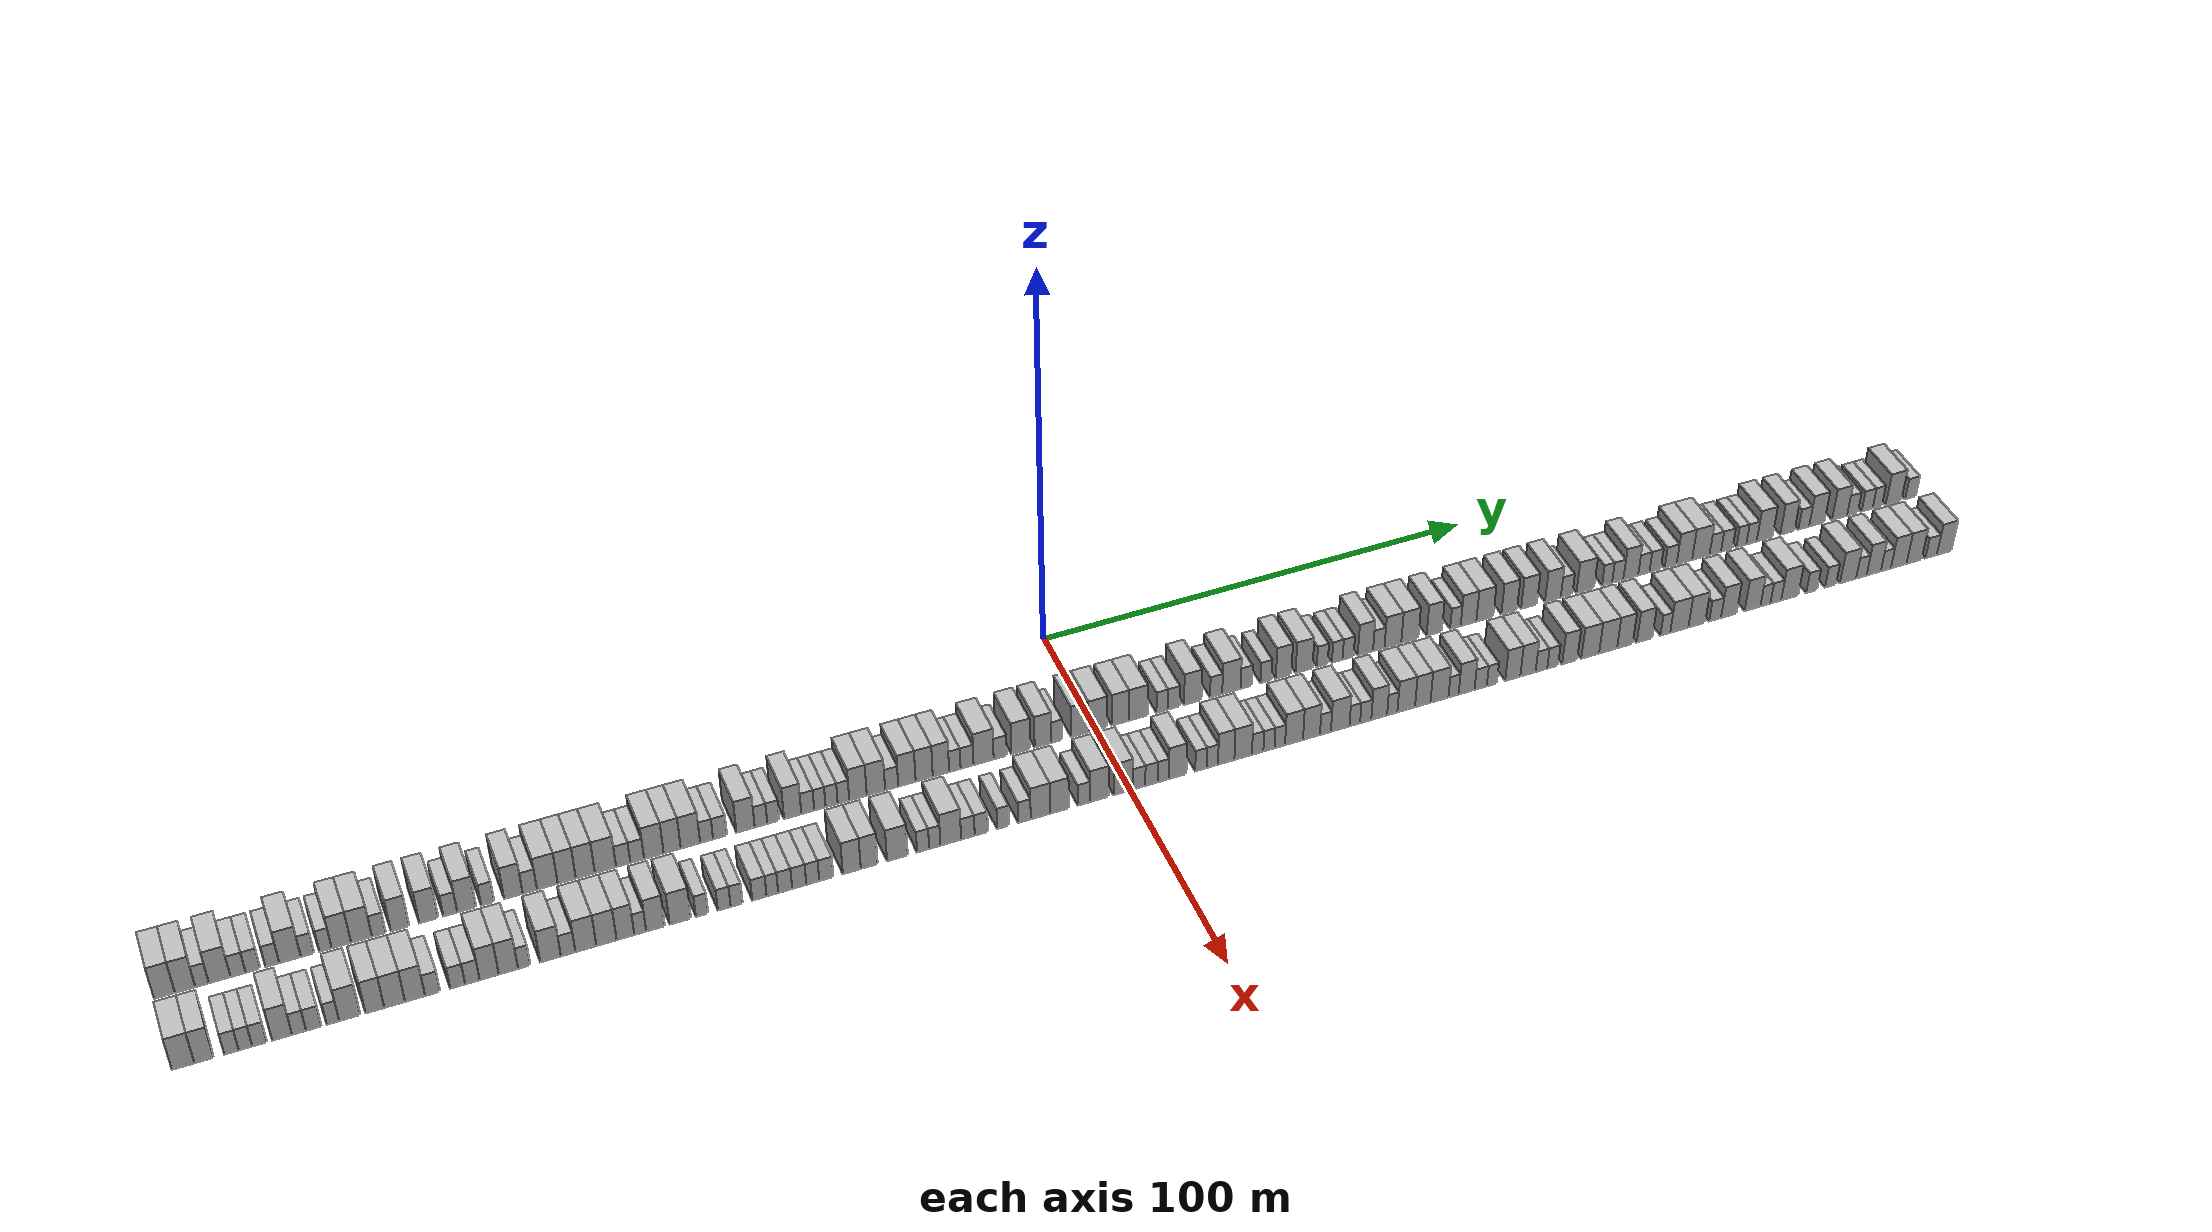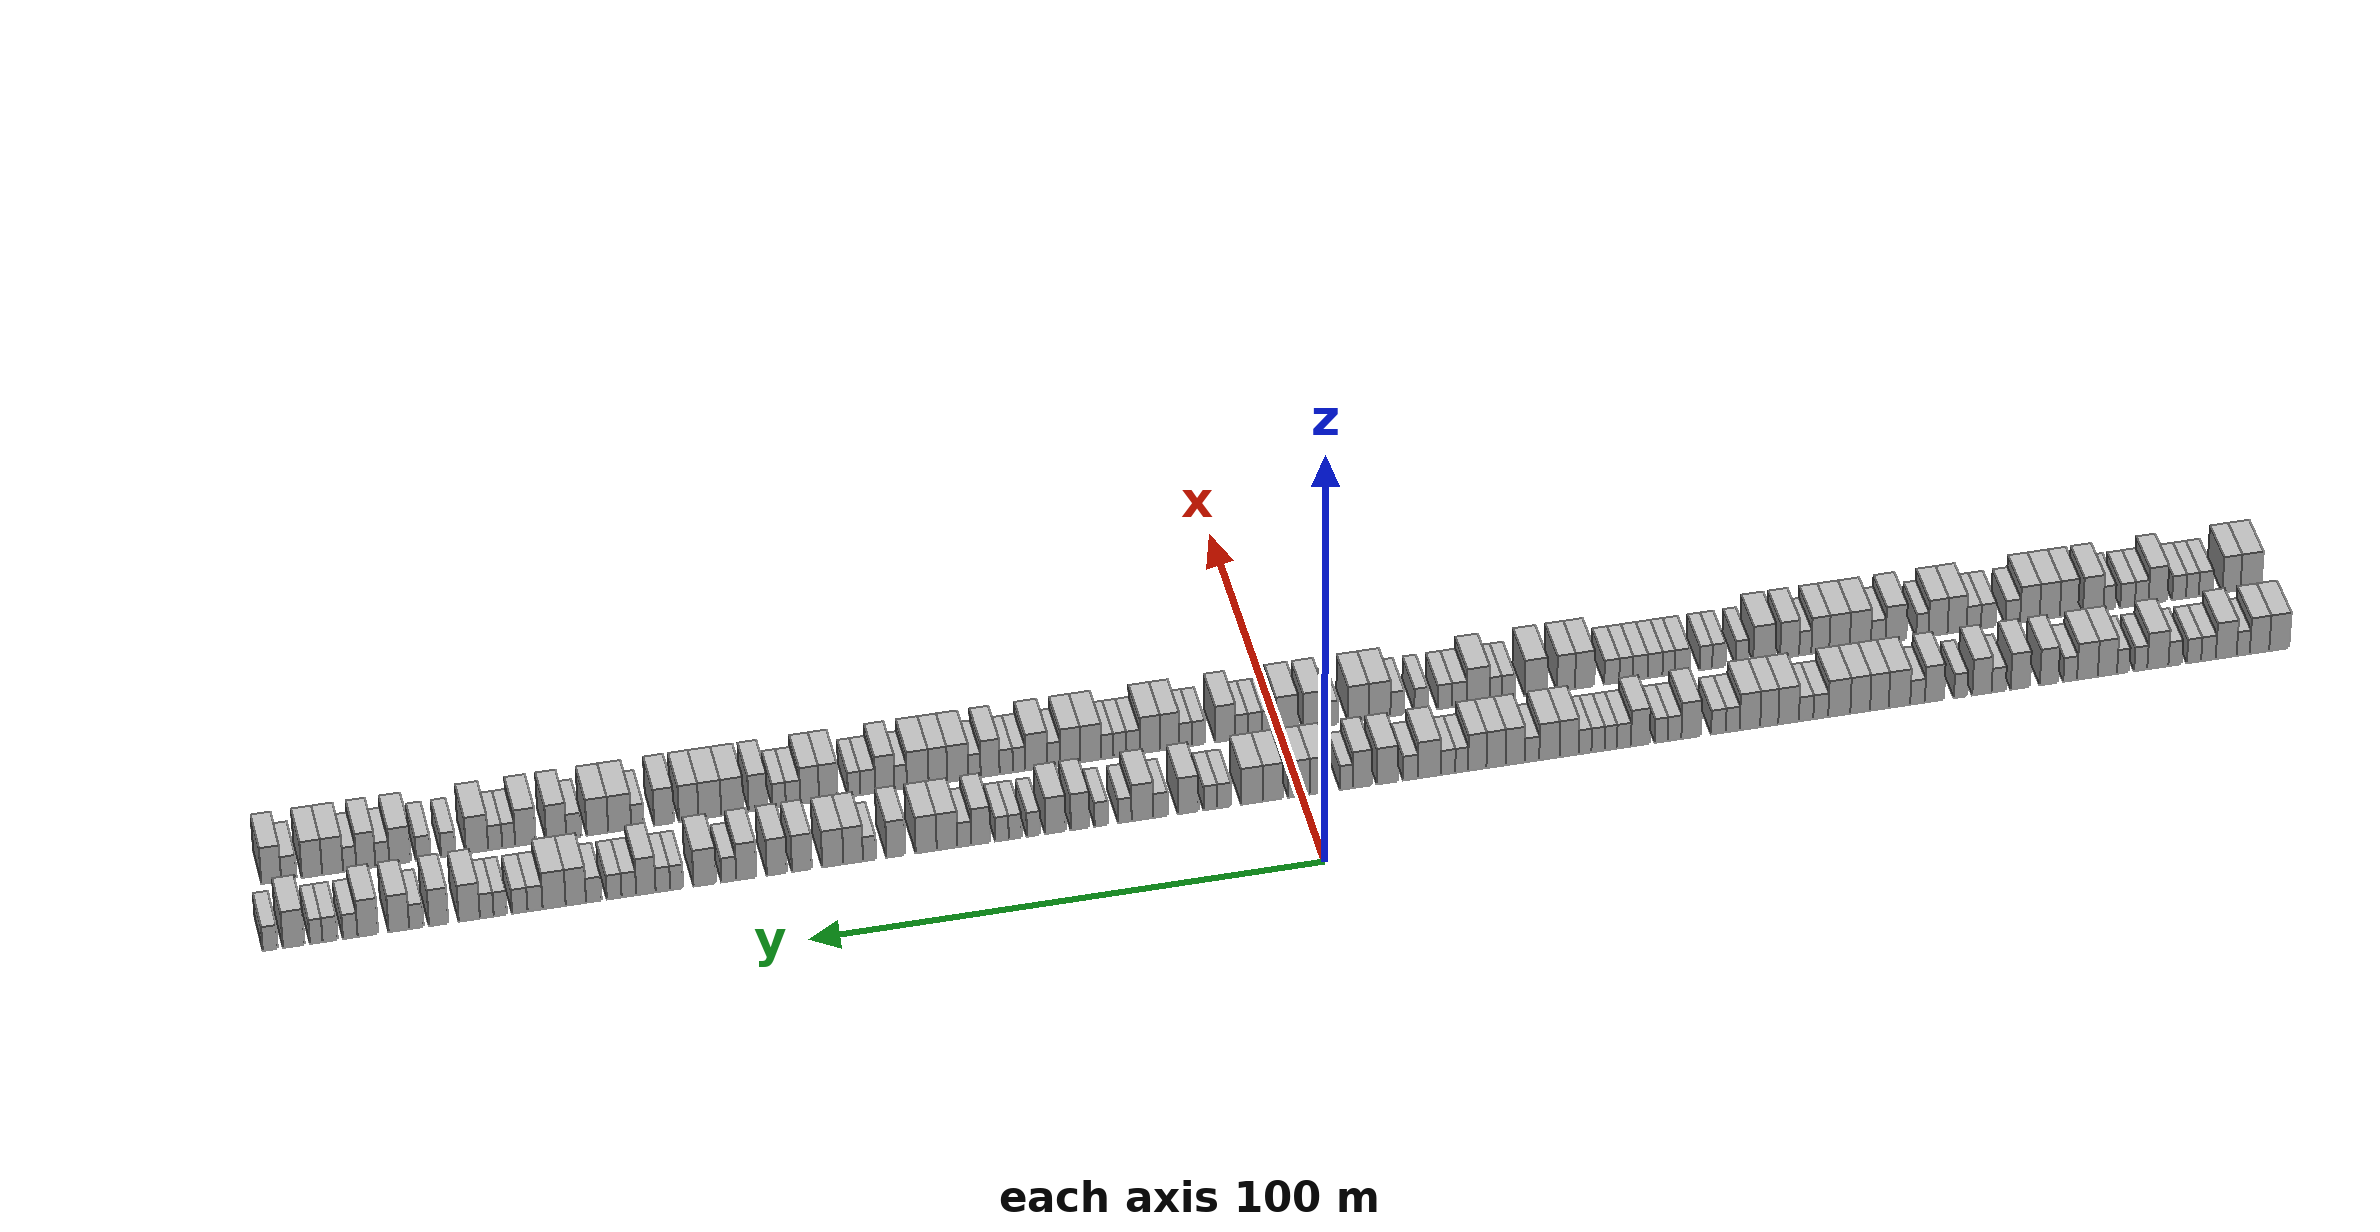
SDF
<sdf version="1.6">
 <world name="default">
  <scene>
   <sky><clouds><speed>12</speed></clouds></sky>
   <ambient>0.4 0.4 0.4 1</ambient>
   <background>0.7 0.7 0.7 1</background>
   <shadows>1</shadows>
  </scene>
  <gravity>0 0 -9.8066</gravity>
  <magnetic_field>6e-06 2.3e-05 -4.2e-05</magnetic_field>
  <physics default="0" name="default_physics" type="ode">
   <ode>
    <solver>
     <type>quick</type>
     <iters>10</iters>
     <sor>1.0</sor>
     <use_dynamic_moi_rescaling>0</use_dynamic_moi_rescaling>
    </solver>
    <constraints>
     <cfm>0</cfm>
     <erp>0.2</erp>
     <contact_max_correcting_vel>100</contact_max_correcting_vel>
     <contact_surface_layer>0.001</contact_surface_layer>
    </constraints>
   </ode>
   <max_step_size>0.004</max_step_size>
   <real_time_factor>1</real_time_factor>
   <real_time_update_rate>250</real_time_update_rate>
  </physics>
  <light name="sun" type="directional">
   <pose>0 0 10 0 0 0</pose>
   <diffuse>0.8 0.8 0.8 1</diffuse>
   <specular>0.2 0.2 0.2 1</specular>
   <attenuation>
    <range>1000</range>
    <constant>0.9</constant>
    <linear>0.01</linear>
    <quadratic>0.001</quadratic>
   </attenuation>
   <direction>-0.5 0.1 -0.9</direction>
  </light>
  <model name="building_1">
   <static>1</static>
   <pose>25.0000 -194.9752 0 0.000000 0.000000 0.000000</pose>
   <link name="link">
    <pose>0 0 4.50 0 0 0</pose>
    <collision name="collision"><geometry><box><size>10.0000 4.0495 9.0000</size></box></geometry></collision>
    <visual name="visual">
     <cast_shadows>0</cast_shadows>
     <geometry><box><size>10.0000 4.0495 9.0000</size></box></geometry>
     <material>
      <script>
       <uri>model://HANNAS_wall/materials/scripts</uri>
       <uri>model://HANNAS_wall/materials/textures</uri>
       <name>vrc/HANNAS_wall</name>
      </script>
     </material>
    </visual>
   </link>
  </model>
  <model name="building_2">
   <static>1</static>
   <pose>25.0000 -190.9780 0 0.000000 0.000000 0.000000</pose>
   <link name="link">
    <pose>0 0 4.50 0 0 0</pose>
    <collision name="collision"><geometry><box><size>10.0000 3.9449 9.0000</size></box></geometry></collision>
    <visual name="visual">
     <cast_shadows>0</cast_shadows>
     <geometry><box><size>10.0000 3.9449 9.0000</size></box></geometry>
     <material>
      <script>
       <uri>model://HANNAS_wall/materials/scripts</uri>
       <uri>model://HANNAS_wall/materials/textures</uri>
       <name>vrc/HANNAS_wall</name>
      </script>
     </material>
    </visual>
   </link>
  </model>
  <model name="building_3">
   <static>1</static>
   <pose>25.0000 -187.6837 0 0.000000 0.000000 0.000000</pose>
   <link name="link">
    <pose>0 0 3.00 0 0 0</pose>
    <collision name="collision"><geometry><box><size>10.0000 2.6437 6.0000</size></box></geometry></collision>
    <visual name="visual">
     <cast_shadows>0</cast_shadows>
     <geometry><box><size>10.0000 2.6437 6.0000</size></box></geometry>
     <material>
      <script>
       <uri>model://HANNAS_wall/materials/scripts</uri>
       <uri>model://HANNAS_wall/materials/textures</uri>
       <name>vrc/HANNAS_wall</name>
      </script>
     </material>
    </visual>
   </link>
  </model>
  <model name="building_4">
   <static>1</static>
   <pose>25.0000 -184.2484 0 0.000000 0.000000 0.000000</pose>
   <link name="link">
    <pose>0 0 4.50 0 0 0</pose>
    <collision name="collision"><geometry><box><size>10.0000 4.2269 9.0000</size></box></geometry></collision>
    <visual name="visual">
     <cast_shadows>0</cast_shadows>
     <geometry><box><size>10.0000 4.2269 9.0000</size></box></geometry>
     <material>
      <script>
       <uri>model://HANNAS_wall/materials/scripts</uri>
       <uri>model://HANNAS_wall/materials/textures</uri>
       <name>vrc/HANNAS_wall</name>
      </script>
     </material>
    </visual>
   </link>
  </model>
  <model name="building_5">
   <static>1</static>
   <pose>25.0000 -180.6615 0 0.000000 0.000000 0.000000</pose>
   <link name="link">
    <pose>0 0 3.00 0 0 0</pose>
    <collision name="collision"><geometry><box><size>10.0000 2.9470 6.0000</size></box></geometry></collision>
    <visual name="visual">
     <cast_shadows>0</cast_shadows>
     <geometry><box><size>10.0000 2.9470 6.0000</size></box></geometry>
     <material>
      <script>
       <uri>model://HANNAS_wall/materials/scripts</uri>
       <uri>model://HANNAS_wall/materials/textures</uri>
       <name>vrc/HANNAS_wall</name>
      </script>
     </material>
    </visual>
   </link>
  </model>
  <model name="building_6">
   <static>1</static>
   <pose>25.0000 -177.7502 0 0.000000 0.000000 0.000000</pose>
   <link name="link">
    <pose>0 0 3.00 0 0 0</pose>
    <collision name="collision"><geometry><box><size>10.0000 2.8756 6.0000</size></box></geometry></collision>
    <visual name="visual">
     <cast_shadows>0</cast_shadows>
     <geometry><box><size>10.0000 2.8756 6.0000</size></box></geometry>
     <material>
      <script>
       <uri>model://HANNAS_wall/materials/scripts</uri>
       <uri>model://HANNAS_wall/materials/textures</uri>
       <name>vrc/HANNAS_wall</name>
      </script>
     </material>
    </visual>
   </link>
  </model>
  <model name="building_7">
   <static>1</static>
   <pose>25.0000 -173.9485 0 0.000000 0.000000 0.000000</pose>
   <link name="link">
    <pose>0 0 3.00 0 0 0</pose>
    <collision name="collision"><geometry><box><size>10.0000 2.7279 6.0000</size></box></geometry></collision>
    <visual name="visual">
     <cast_shadows>0</cast_shadows>
     <geometry><box><size>10.0000 2.7279 6.0000</size></box></geometry>
     <material>
      <script>
       <uri>model://HANNAS_wall/materials/scripts</uri>
       <uri>model://HANNAS_wall/materials/textures</uri>
       <name>vrc/HANNAS_wall</name>
      </script>
     </material>
    </visual>
   </link>
  </model>
  <model name="building_8">
   <static>1</static>
   <pose>25.0000 -170.4557 0 0.000000 0.000000 0.000000</pose>
   <link name="link">
    <pose>0 0 4.50 0 0 0</pose>
    <collision name="collision"><geometry><box><size>10.0000 4.2579 9.0000</size></box></geometry></collision>
    <visual name="visual">
     <cast_shadows>0</cast_shadows>
     <geometry><box><size>10.0000 4.2579 9.0000</size></box></geometry>
     <material>
      <script>
       <uri>model://HANNAS_wall/materials/scripts</uri>
       <uri>model://HANNAS_wall/materials/textures</uri>
       <name>vrc/HANNAS_wall</name>
      </script>
     </material>
    </visual>
   </link>
  </model>
  <model name="building_9">
   <static>1</static>
   <pose>25.0000 -167.0054 0 0.000000 0.000000 0.000000</pose>
   <link name="link">
    <pose>0 0 3.00 0 0 0</pose>
    <collision name="collision"><geometry><box><size>10.0000 2.6426 6.0000</size></box></geometry></collision>
    <visual name="visual">
     <cast_shadows>0</cast_shadows>
     <geometry><box><size>10.0000 2.6426 6.0000</size></box></geometry>
     <material>
      <script>
       <uri>model://HANNAS_wall/materials/scripts</uri>
       <uri>model://HANNAS_wall/materials/textures</uri>
       <name>vrc/HANNAS_wall</name>
      </script>
     </material>
    </visual>
   </link>
  </model>
  <model name="building_10">
   <static>1</static>
   <pose>25.0000 -163.4575 0 0.000000 0.000000 0.000000</pose>
   <link name="link">
    <pose>0 0 3.00 0 0 0</pose>
    <collision name="collision"><geometry><box><size>10.0000 2.4532 6.0000</size></box></geometry></collision>
    <visual name="visual">
     <cast_shadows>0</cast_shadows>
     <geometry><box><size>10.0000 2.4532 6.0000</size></box></geometry>
     <material>
      <script>
       <uri>model://HANNAS_wall/materials/scripts</uri>
       <uri>model://HANNAS_wall/materials/textures</uri>
       <name>vrc/HANNAS_wall</name>
      </script>
     </material>
    </visual>
   </link>
  </model>
  <model name="building_11">
   <static>1</static>
   <pose>25.0000 -160.2927 0 0.000000 0.000000 0.000000</pose>
   <link name="link">
    <pose>0 0 4.50 0 0 0</pose>
    <collision name="collision"><geometry><box><size>10.0000 3.8765 9.0000</size></box></geometry></collision>
    <visual name="visual">
     <cast_shadows>0</cast_shadows>
     <geometry><box><size>10.0000 3.8765 9.0000</size></box></geometry>
     <material>
      <script>
       <uri>model://HANNAS_wall/materials/scripts</uri>
       <uri>model://HANNAS_wall/materials/textures</uri>
       <name>vrc/HANNAS_wall</name>
      </script>
     </material>
    </visual>
   </link>
  </model>
  <model name="building_12">
   <static>1</static>
   <pose>25.0000 -156.2672 0 0.000000 0.000000 0.000000</pose>
   <link name="link">
    <pose>0 0 4.50 0 0 0</pose>
    <collision name="collision"><geometry><box><size>10.0000 4.1745 9.0000</size></box></geometry></collision>
    <visual name="visual">
     <cast_shadows>0</cast_shadows>
     <geometry><box><size>10.0000 4.1745 9.0000</size></box></geometry>
     <material>
      <script>
       <uri>model://HANNAS_wall/materials/scripts</uri>
       <uri>model://HANNAS_wall/materials/textures</uri>
       <name>vrc/HANNAS_wall</name>
      </script>
     </material>
    </visual>
   </link>
  </model>
  <model name="building_13">
   <static>1</static>
   <pose>25.0000 -152.7964 0 0.000000 0.000000 0.000000</pose>
   <link name="link">
    <pose>0 0 3.00 0 0 0</pose>
    <collision name="collision"><geometry><box><size>10.0000 2.7671 6.0000</size></box></geometry></collision>
    <visual name="visual">
     <cast_shadows>0</cast_shadows>
     <geometry><box><size>10.0000 2.7671 6.0000</size></box></geometry>
     <material>
      <script>
       <uri>model://HANNAS_wall/materials/scripts</uri>
       <uri>model://HANNAS_wall/materials/textures</uri>
       <name>vrc/HANNAS_wall</name>
      </script>
     </material>
    </visual>
   </link>
  </model>
  <model name="building_14">
   <static>1</static>
   <pose>25.0000 -148.5535 0 0.000000 0.000000 0.000000</pose>
   <link name="link">
    <pose>0 0 4.50 0 0 0</pose>
    <collision name="collision"><geometry><box><size>10.0000 3.7188 9.0000</size></box></geometry></collision>
    <visual name="visual">
     <cast_shadows>0</cast_shadows>
     <geometry><box><size>10.0000 3.7188 9.0000</size></box></geometry>
     <material>
      <script>
       <uri>model://HANNAS_wall/materials/scripts</uri>
       <uri>model://HANNAS_wall/materials/textures</uri>
       <name>vrc/HANNAS_wall</name>
      </script>
     </material>
    </visual>
   </link>
  </model>
  <model name="building_15">
   <static>1</static>
   <pose>25.0000 -142.7608 0 0.000000 0.000000 0.000000</pose>
   <link name="link">
    <pose>0 0 4.50 0 0 0</pose>
    <collision name="collision"><geometry><box><size>10.0000 3.8666 9.0000</size></box></geometry></collision>
    <visual name="visual">
     <cast_shadows>0</cast_shadows>
     <geometry><box><size>10.0000 3.8666 9.0000</size></box></geometry>
     <material>
      <script>
       <uri>model://HANNAS_wall/materials/scripts</uri>
       <uri>model://HANNAS_wall/materials/textures</uri>
       <name>vrc/HANNAS_wall</name>
      </script>
     </material>
    </visual>
   </link>
  </model>
  <model name="building_16">
   <static>1</static>
   <pose>25.0000 -138.4152 0 0.000000 0.000000 0.000000</pose>
   <link name="link">
    <pose>0 0 3.00 0 0 0</pose>
    <collision name="collision"><geometry><box><size>10.0000 2.8246 6.0000</size></box></geometry></collision>
    <visual name="visual">
     <cast_shadows>0</cast_shadows>
     <geometry><box><size>10.0000 2.8246 6.0000</size></box></geometry>
     <material>
      <script>
       <uri>model://HANNAS_wall/materials/scripts</uri>
       <uri>model://HANNAS_wall/materials/textures</uri>
       <name>vrc/HANNAS_wall</name>
      </script>
     </material>
    </visual>
   </link>
  </model>
  <model name="building_17">
   <static>1</static>
   <pose>25.0000 -135.0712 0 0.000000 0.000000 0.000000</pose>
   <link name="link">
    <pose>0 0 4.50 0 0 0</pose>
    <collision name="collision"><geometry><box><size>10.0000 3.8633 9.0000</size></box></geometry></collision>
    <visual name="visual">
     <cast_shadows>0</cast_shadows>
     <geometry><box><size>10.0000 3.8633 9.0000</size></box></geometry>
     <material>
      <script>
       <uri>model://HANNAS_wall/materials/scripts</uri>
       <uri>model://HANNAS_wall/materials/textures</uri>
       <name>vrc/HANNAS_wall</name>
      </script>
     </material>
    </visual>
   </link>
  </model>
  <model name="building_18">
   <static>1</static>
   <pose>25.0000 -130.7995 0 0.000000 0.000000 0.000000</pose>
   <link name="link">
    <pose>0 0 3.00 0 0 0</pose>
    <collision name="collision"><geometry><box><size>10.0000 2.6801 6.0000</size></box></geometry></collision>
    <visual name="visual">
     <cast_shadows>0</cast_shadows>
     <geometry><box><size>10.0000 2.6801 6.0000</size></box></geometry>
     <material>
      <script>
       <uri>model://HANNAS_wall/materials/scripts</uri>
       <uri>model://HANNAS_wall/materials/textures</uri>
       <name>vrc/HANNAS_wall</name>
      </script>
     </material>
    </visual>
   </link>
  </model>
  <model name="building_19">
   <static>1</static>
   <pose>25.0000 -125.5500 0 0.000000 0.000000 0.000000</pose>
   <link name="link">
    <pose>0 0 4.50 0 0 0</pose>
    <collision name="collision"><geometry><box><size>10.0000 3.8190 9.0000</size></box></geometry></collision>
    <visual name="visual">
     <cast_shadows>0</cast_shadows>
     <geometry><box><size>10.0000 3.8190 9.0000</size></box></geometry>
     <material>
      <script>
       <uri>model://HANNAS_wall/materials/scripts</uri>
       <uri>model://HANNAS_wall/materials/textures</uri>
       <name>vrc/HANNAS_wall</name>
      </script>
     </material>
    </visual>
   </link>
  </model>
  <model name="building_20">
   <static>1</static>
   <pose>25.0000 -122.1705 0 0.000000 0.000000 0.000000</pose>
   <link name="link">
    <pose>0 0 3.00 0 0 0</pose>
    <collision name="collision"><geometry><box><size>10.0000 2.9399 6.0000</size></box></geometry></collision>
    <visual name="visual">
     <cast_shadows>0</cast_shadows>
     <geometry><box><size>10.0000 2.9399 6.0000</size></box></geometry>
     <material>
      <script>
       <uri>model://HANNAS_wall/materials/scripts</uri>
       <uri>model://HANNAS_wall/materials/textures</uri>
       <name>vrc/HANNAS_wall</name>
      </script>
     </material>
    </visual>
   </link>
  </model>
  <model name="building_21">
   <static>1</static>
   <pose>25.0000 -118.5584 0 0.000000 0.000000 0.000000</pose>
   <link name="link">
    <pose>0 0 4.50 0 0 0</pose>
    <collision name="collision"><geometry><box><size>10.0000 4.2843 9.0000</size></box></geometry></collision>
    <visual name="visual">
     <cast_shadows>0</cast_shadows>
     <geometry><box><size>10.0000 4.2843 9.0000</size></box></geometry>
     <material>
      <script>
       <uri>model://HANNAS_wall/materials/scripts</uri>
       <uri>model://HANNAS_wall/materials/textures</uri>
       <name>vrc/HANNAS_wall</name>
      </script>
     </material>
    </visual>
   </link>
  </model>
  <model name="building_22">
   <static>1</static>
   <pose>25.0000 -114.5460 0 0.000000 0.000000 0.000000</pose>
   <link name="link">
    <pose>0 0 4.50 0 0 0</pose>
    <collision name="collision"><geometry><box><size>10.0000 3.7405 9.0000</size></box></geometry></collision>
    <visual name="visual">
     <cast_shadows>0</cast_shadows>
     <geometry><box><size>10.0000 3.7405 9.0000</size></box></geometry>
     <material>
      <script>
       <uri>model://HANNAS_wall/materials/scripts</uri>
       <uri>model://HANNAS_wall/materials/textures</uri>
       <name>vrc/HANNAS_wall</name>
      </script>
     </material>
    </visual>
   </link>
  </model>
  <model name="building_23">
   <static>1</static>
   <pose>25.0000 -110.7014 0 0.000000 0.000000 0.000000</pose>
   <link name="link">
    <pose>0 0 4.50 0 0 0</pose>
    <collision name="collision"><geometry><box><size>10.0000 3.9487 9.0000</size></box></geometry></collision>
    <visual name="visual">
     <cast_shadows>0</cast_shadows>
     <geometry><box><size>10.0000 3.9487 9.0000</size></box></geometry>
     <material>
      <script>
       <uri>model://HANNAS_wall/materials/scripts</uri>
       <uri>model://HANNAS_wall/materials/textures</uri>
       <name>vrc/HANNAS_wall</name>
      </script>
     </material>
    </visual>
   </link>
  </model>
  <model name="building_24">
   <static>1</static>
   <pose>25.0000 -106.5193 0 0.000000 0.000000 0.000000</pose>
   <link name="link">
    <pose>0 0 4.50 0 0 0</pose>
    <collision name="collision"><geometry><box><size>10.0000 4.4155 9.0000</size></box></geometry></collision>
    <visual name="visual">
     <cast_shadows>0</cast_shadows>
     <geometry><box><size>10.0000 4.4155 9.0000</size></box></geometry>
     <material>
      <script>
       <uri>model://HANNAS_wall/materials/scripts</uri>
       <uri>model://HANNAS_wall/materials/textures</uri>
       <name>vrc/HANNAS_wall</name>
      </script>
     </material>
    </visual>
   </link>
  </model>
  <model name="building_25">
   <static>1</static>
   <pose>25.0000 -102.8213 0 0.000000 0.000000 0.000000</pose>
   <link name="link">
    <pose>0 0 3.00 0 0 0</pose>
    <collision name="collision"><geometry><box><size>10.0000 2.9803 6.0000</size></box></geometry></collision>
    <visual name="visual">
     <cast_shadows>0</cast_shadows>
     <geometry><box><size>10.0000 2.9803 6.0000</size></box></geometry>
     <material>
      <script>
       <uri>model://HANNAS_wall/materials/scripts</uri>
       <uri>model://HANNAS_wall/materials/textures</uri>
       <name>vrc/HANNAS_wall</name>
      </script>
     </material>
    </visual>
   </link>
  </model>
  <model name="building_26">
   <static>1</static>
   <pose>25.0000 -99.8959 0 0.000000 0.000000 0.000000</pose>
   <link name="link">
    <pose>0 0 3.00 0 0 0</pose>
    <collision name="collision"><geometry><box><size>10.0000 2.8706 6.0000</size></box></geometry></collision>
    <visual name="visual">
     <cast_shadows>0</cast_shadows>
     <geometry><box><size>10.0000 2.8706 6.0000</size></box></geometry>
     <material>
      <script>
       <uri>model://HANNAS_wall/materials/scripts</uri>
       <uri>model://HANNAS_wall/materials/textures</uri>
       <name>vrc/HANNAS_wall</name>
      </script>
     </material>
    </visual>
   </link>
  </model>
  <model name="building_27">
   <static>1</static>
   <pose>25.0000 -96.4056 0 0.000000 0.000000 0.000000</pose>
   <link name="link">
    <pose>0 0 4.50 0 0 0</pose>
    <collision name="collision"><geometry><box><size>10.0000 4.1100 9.0000</size></box></geometry></collision>
    <visual name="visual">
     <cast_shadows>0</cast_shadows>
     <geometry><box><size>10.0000 4.1100 9.0000</size></box></geometry>
     <material>
      <script>
       <uri>model://HANNAS_wall/materials/scripts</uri>
       <uri>model://HANNAS_wall/materials/textures</uri>
       <name>vrc/HANNAS_wall</name>
      </script>
     </material>
    </visual>
   </link>
  </model>
  <model name="building_28">
   <static>1</static>
   <pose>25.0000 -92.5490 0 0.000000 0.000000 0.000000</pose>
   <link name="link">
    <pose>0 0 4.50 0 0 0</pose>
    <collision name="collision"><geometry><box><size>10.0000 3.6030 9.0000</size></box></geometry></collision>
    <visual name="visual">
     <cast_shadows>0</cast_shadows>
     <geometry><box><size>10.0000 3.6030 9.0000</size></box></geometry>
     <material>
      <script>
       <uri>model://HANNAS_wall/materials/scripts</uri>
       <uri>model://HANNAS_wall/materials/textures</uri>
       <name>vrc/HANNAS_wall</name>
      </script>
     </material>
    </visual>
   </link>
  </model>
  <model name="building_29">
   <static>1</static>
   <pose>25.0000 -88.7035 0 0.000000 0.000000 0.000000</pose>
   <link name="link">
    <pose>0 0 4.50 0 0 0</pose>
    <collision name="collision"><geometry><box><size>10.0000 4.0882 9.0000</size></box></geometry></collision>
    <visual name="visual">
     <cast_shadows>0</cast_shadows>
     <geometry><box><size>10.0000 4.0882 9.0000</size></box></geometry>
     <material>
      <script>
       <uri>model://HANNAS_wall/materials/scripts</uri>
       <uri>model://HANNAS_wall/materials/textures</uri>
       <name>vrc/HANNAS_wall</name>
      </script>
     </material>
    </visual>
   </link>
  </model>
  <model name="building_30">
   <static>1</static>
   <pose>25.0000 -85.2844 0 0.000000 0.000000 0.000000</pose>
   <link name="link">
    <pose>0 0 3.00 0 0 0</pose>
    <collision name="collision"><geometry><box><size>10.0000 2.7500 6.0000</size></box></geometry></collision>
    <visual name="visual">
     <cast_shadows>0</cast_shadows>
     <geometry><box><size>10.0000 2.7500 6.0000</size></box></geometry>
     <material>
      <script>
       <uri>model://HANNAS_wall/materials/scripts</uri>
       <uri>model://HANNAS_wall/materials/textures</uri>
       <name>vrc/HANNAS_wall</name>
      </script>
     </material>
    </visual>
   </link>
  </model>
  <model name="building_31">
   <static>1</static>
   <pose>25.0000 -82.4349 0 0.000000 0.000000 0.000000</pose>
   <link name="link">
    <pose>0 0 3.00 0 0 0</pose>
    <collision name="collision"><geometry><box><size>10.0000 2.9490 6.0000</size></box></geometry></collision>
    <visual name="visual">
     <cast_shadows>0</cast_shadows>
     <geometry><box><size>10.0000 2.9490 6.0000</size></box></geometry>
     <material>
      <script>
       <uri>model://HANNAS_wall/materials/scripts</uri>
       <uri>model://HANNAS_wall/materials/textures</uri>
       <name>vrc/HANNAS_wall</name>
      </script>
     </material>
    </visual>
   </link>
  </model>
  <model name="building_32">
   <static>1</static>
   <pose>25.0000 -77.0061 0 0.000000 0.000000 0.000000</pose>
   <link name="link">
    <pose>0 0 4.50 0 0 0</pose>
    <collision name="collision"><geometry><box><size>10.0000 3.9085 9.0000</size></box></geometry></collision>
    <visual name="visual">
     <cast_shadows>0</cast_shadows>
     <geometry><box><size>10.0000 3.9085 9.0000</size></box></geometry>
     <material>
      <script>
       <uri>model://HANNAS_wall/materials/scripts</uri>
       <uri>model://HANNAS_wall/materials/textures</uri>
       <name>vrc/HANNAS_wall</name>
      </script>
     </material>
    </visual>
   </link>
  </model>
  <model name="building_33">
   <static>1</static>
   <pose>25.0000 -73.7055 0 0.000000 0.000000 0.000000</pose>
   <link name="link">
    <pose>0 0 3.00 0 0 0</pose>
    <collision name="collision"><geometry><box><size>10.0000 2.6928 6.0000</size></box></geometry></collision>
    <visual name="visual">
     <cast_shadows>0</cast_shadows>
     <geometry><box><size>10.0000 2.6928 6.0000</size></box></geometry>
     <material>
      <script>
       <uri>model://HANNAS_wall/materials/scripts</uri>
       <uri>model://HANNAS_wall/materials/textures</uri>
       <name>vrc/HANNAS_wall</name>
      </script>
     </material>
    </visual>
   </link>
  </model>
  <model name="building_34">
   <static>1</static>
   <pose>25.0000 -71.0634 0 0.000000 0.000000 0.000000</pose>
   <link name="link">
    <pose>0 0 3.00 0 0 0</pose>
    <collision name="collision"><geometry><box><size>10.0000 2.5914 6.0000</size></box></geometry></collision>
    <visual name="visual">
     <cast_shadows>0</cast_shadows>
     <geometry><box><size>10.0000 2.5914 6.0000</size></box></geometry>
     <material>
      <script>
       <uri>model://HANNAS_wall/materials/scripts</uri>
       <uri>model://HANNAS_wall/materials/textures</uri>
       <name>vrc/HANNAS_wall</name>
      </script>
     </material>
    </visual>
   </link>
  </model>
  <model name="building_35">
   <static>1</static>
   <pose>25.0000 -66.9043 0 0.000000 0.000000 0.000000</pose>
   <link name="link">
    <pose>0 0 4.50 0 0 0</pose>
    <collision name="collision"><geometry><box><size>10.0000 3.7268 9.0000</size></box></geometry></collision>
    <visual name="visual">
     <cast_shadows>0</cast_shadows>
     <geometry><box><size>10.0000 3.7268 9.0000</size></box></geometry>
     <material>
      <script>
       <uri>model://HANNAS_wall/materials/scripts</uri>
       <uri>model://HANNAS_wall/materials/textures</uri>
       <name>vrc/HANNAS_wall</name>
      </script>
     </material>
    </visual>
   </link>
  </model>
  <model name="building_36">
   <static>1</static>
   <pose>25.0000 -63.6549 0 0.000000 0.000000 0.000000</pose>
   <link name="link">
    <pose>0 0 3.00 0 0 0</pose>
    <collision name="collision"><geometry><box><size>10.0000 2.7721 6.0000</size></box></geometry></collision>
    <visual name="visual">
     <cast_shadows>0</cast_shadows>
     <geometry><box><size>10.0000 2.7721 6.0000</size></box></geometry>
     <material>
      <script>
       <uri>model://HANNAS_wall/materials/scripts</uri>
       <uri>model://HANNAS_wall/materials/textures</uri>
       <name>vrc/HANNAS_wall</name>
      </script>
     </material>
    </visual>
   </link>
  </model>
  <model name="building_37">
   <static>1</static>
   <pose>25.0000 -61.0405 0 0.000000 0.000000 0.000000</pose>
   <link name="link">
    <pose>0 0 3.00 0 0 0</pose>
    <collision name="collision"><geometry><box><size>10.0000 2.4567 6.0000</size></box></geometry></collision>
    <visual name="visual">
     <cast_shadows>0</cast_shadows>
     <geometry><box><size>10.0000 2.4567 6.0000</size></box></geometry>
     <material>
      <script>
       <uri>model://HANNAS_wall/materials/scripts</uri>
       <uri>model://HANNAS_wall/materials/textures</uri>
       <name>vrc/HANNAS_wall</name>
      </script>
     </material>
    </visual>
   </link>
  </model>
  <model name="building_38">
   <static>1</static>
   <pose>25.0000 -58.5033 0 0.000000 0.000000 0.000000</pose>
   <link name="link">
    <pose>0 0 3.00 0 0 0</pose>
    <collision name="collision"><geometry><box><size>10.0000 2.6177 6.0000</size></box></geometry></collision>
    <visual name="visual">
     <cast_shadows>0</cast_shadows>
     <geometry><box><size>10.0000 2.6177 6.0000</size></box></geometry>
     <material>
      <script>
       <uri>model://HANNAS_wall/materials/scripts</uri>
       <uri>model://HANNAS_wall/materials/textures</uri>
       <name>vrc/HANNAS_wall</name>
      </script>
     </material>
    </visual>
   </link>
  </model>
  <model name="building_39">
   <static>1</static>
   <pose>25.0000 -55.9374 0 0.000000 0.000000 0.000000</pose>
   <link name="link">
    <pose>0 0 3.00 0 0 0</pose>
    <collision name="collision"><geometry><box><size>10.0000 2.5140 6.0000</size></box></geometry></collision>
    <visual name="visual">
     <cast_shadows>0</cast_shadows>
     <geometry><box><size>10.0000 2.5140 6.0000</size></box></geometry>
     <material>
      <script>
       <uri>model://HANNAS_wall/materials/scripts</uri>
       <uri>model://HANNAS_wall/materials/textures</uri>
       <name>vrc/HANNAS_wall</name>
      </script>
     </material>
    </visual>
   </link>
  </model>
  <model name="building_40">
   <static>1</static>
   <pose>25.0000 -52.7762 0 0.000000 0.000000 0.000000</pose>
   <link name="link">
    <pose>0 0 4.50 0 0 0</pose>
    <collision name="collision"><geometry><box><size>10.0000 3.8085 9.0000</size></box></geometry></collision>
    <visual name="visual">
     <cast_shadows>0</cast_shadows>
     <geometry><box><size>10.0000 3.8085 9.0000</size></box></geometry>
     <material>
      <script>
       <uri>model://HANNAS_wall/materials/scripts</uri>
       <uri>model://HANNAS_wall/materials/textures</uri>
       <name>vrc/HANNAS_wall</name>
      </script>
     </material>
    </visual>
   </link>
  </model>
  <model name="building_41">
   <static>1</static>
   <pose>25.0000 -48.8694 0 0.000000 0.000000 0.000000</pose>
   <link name="link">
    <pose>0 0 4.50 0 0 0</pose>
    <collision name="collision"><geometry><box><size>10.0000 4.0051 9.0000</size></box></geometry></collision>
    <visual name="visual">
     <cast_shadows>0</cast_shadows>
     <geometry><box><size>10.0000 4.0051 9.0000</size></box></geometry>
     <material>
      <script>
       <uri>model://HANNAS_wall/materials/scripts</uri>
       <uri>model://HANNAS_wall/materials/textures</uri>
       <name>vrc/HANNAS_wall</name>
      </script>
     </material>
    </visual>
   </link>
  </model>
  <model name="building_42">
   <static>1</static>
   <pose>25.0000 -45.4330 0 0.000000 0.000000 0.000000</pose>
   <link name="link">
    <pose>0 0 3.00 0 0 0</pose>
    <collision name="collision"><geometry><box><size>10.0000 2.8677 6.0000</size></box></geometry></collision>
    <visual name="visual">
     <cast_shadows>0</cast_shadows>
     <geometry><box><size>10.0000 2.8677 6.0000</size></box></geometry>
     <material>
      <script>
       <uri>model://HANNAS_wall/materials/scripts</uri>
       <uri>model://HANNAS_wall/materials/textures</uri>
       <name>vrc/HANNAS_wall</name>
      </script>
     </material>
    </visual>
   </link>
  </model>
  <model name="building_43">
   <static>1</static>
   <pose>25.0000 -42.0925 0 0.000000 0.000000 0.000000</pose>
   <link name="link">
    <pose>0 0 4.50 0 0 0</pose>
    <collision name="collision"><geometry><box><size>10.0000 3.8132 9.0000</size></box></geometry></collision>
    <visual name="visual">
     <cast_shadows>0</cast_shadows>
     <geometry><box><size>10.0000 3.8132 9.0000</size></box></geometry>
     <material>
      <script>
       <uri>model://HANNAS_wall/materials/scripts</uri>
       <uri>model://HANNAS_wall/materials/textures</uri>
       <name>vrc/HANNAS_wall</name>
      </script>
     </material>
    </visual>
   </link>
  </model>
  <model name="building_44">
   <static>1</static>
   <pose>25.0000 -38.3010 0 0.000000 0.000000 0.000000</pose>
   <link name="link">
    <pose>0 0 4.50 0 0 0</pose>
    <collision name="collision"><geometry><box><size>10.0000 3.7698 9.0000</size></box></geometry></collision>
    <visual name="visual">
     <cast_shadows>0</cast_shadows>
     <geometry><box><size>10.0000 3.7698 9.0000</size></box></geometry>
     <material>
      <script>
       <uri>model://HANNAS_wall/materials/scripts</uri>
       <uri>model://HANNAS_wall/materials/textures</uri>
       <name>vrc/HANNAS_wall</name>
      </script>
     </material>
    </visual>
   </link>
  </model>
  <model name="building_45">
   <static>1</static>
   <pose>25.0000 -34.6114 0 0.000000 0.000000 0.000000</pose>
   <link name="link">
    <pose>0 0 4.50 0 0 0</pose>
    <collision name="collision"><geometry><box><size>10.0000 3.6094 9.0000</size></box></geometry></collision>
    <visual name="visual">
     <cast_shadows>0</cast_shadows>
     <geometry><box><size>10.0000 3.6094 9.0000</size></box></geometry>
     <material>
      <script>
       <uri>model://HANNAS_wall/materials/scripts</uri>
       <uri>model://HANNAS_wall/materials/textures</uri>
       <name>vrc/HANNAS_wall</name>
      </script>
     </material>
    </visual>
   </link>
  </model>
  <model name="building_46">
   <static>1</static>
   <pose>25.0000 -31.5375 0 0.000000 0.000000 0.000000</pose>
   <link name="link">
    <pose>0 0 3.00 0 0 0</pose>
    <collision name="collision"><geometry><box><size>10.0000 2.5385 6.0000</size></box></geometry></collision>
    <visual name="visual">
     <cast_shadows>0</cast_shadows>
     <geometry><box><size>10.0000 2.5385 6.0000</size></box></geometry>
     <material>
      <script>
       <uri>model://HANNAS_wall/materials/scripts</uri>
       <uri>model://HANNAS_wall/materials/textures</uri>
       <name>vrc/HANNAS_wall</name>
      </script>
     </material>
    </visual>
   </link>
  </model>
  <model name="building_47">
   <static>1</static>
   <pose>25.0000 -28.8306 0 0.000000 0.000000 0.000000</pose>
   <link name="link">
    <pose>0 0 3.00 0 0 0</pose>
    <collision name="collision"><geometry><box><size>10.0000 2.8753 6.0000</size></box></geometry></collision>
    <visual name="visual">
     <cast_shadows>0</cast_shadows>
     <geometry><box><size>10.0000 2.8753 6.0000</size></box></geometry>
     <material>
      <script>
       <uri>model://HANNAS_wall/materials/scripts</uri>
       <uri>model://HANNAS_wall/materials/textures</uri>
       <name>vrc/HANNAS_wall</name>
      </script>
     </material>
    </visual>
   </link>
  </model>
  <model name="building_48">
   <static>1</static>
   <pose>25.0000 -25.1582 0 0.000000 0.000000 0.000000</pose>
   <link name="link">
    <pose>0 0 4.50 0 0 0</pose>
    <collision name="collision"><geometry><box><size>10.0000 4.4695 9.0000</size></box></geometry></collision>
    <visual name="visual">
     <cast_shadows>0</cast_shadows>
     <geometry><box><size>10.0000 4.4695 9.0000</size></box></geometry>
     <material>
      <script>
       <uri>model://HANNAS_wall/materials/scripts</uri>
       <uri>model://HANNAS_wall/materials/textures</uri>
       <name>vrc/HANNAS_wall</name>
      </script>
     </material>
    </visual>
   </link>
  </model>
  <model name="building_49">
   <static>1</static>
   <pose>25.0000 -21.4547 0 0.000000 0.000000 0.000000</pose>
   <link name="link">
    <pose>0 0 3.00 0 0 0</pose>
    <collision name="collision"><geometry><box><size>10.0000 2.9375 6.0000</size></box></geometry></collision>
    <visual name="visual">
     <cast_shadows>0</cast_shadows>
     <geometry><box><size>10.0000 2.9375 6.0000</size></box></geometry>
     <material>
      <script>
       <uri>model://HANNAS_wall/materials/scripts</uri>
       <uri>model://HANNAS_wall/materials/textures</uri>
       <name>vrc/HANNAS_wall</name>
      </script>
     </material>
    </visual>
   </link>
  </model>
  <model name="building_50">
   <static>1</static>
   <pose>25.0000 -16.8715 0 0.000000 0.000000 0.000000</pose>
   <link name="link">
    <pose>0 0 4.50 0 0 0</pose>
    <collision name="collision"><geometry><box><size>10.0000 4.2289 9.0000</size></box></geometry></collision>
    <visual name="visual">
     <cast_shadows>0</cast_shadows>
     <geometry><box><size>10.0000 4.2289 9.0000</size></box></geometry>
     <material>
      <script>
       <uri>model://HANNAS_wall/materials/scripts</uri>
       <uri>model://HANNAS_wall/materials/textures</uri>
       <name>vrc/HANNAS_wall</name>
      </script>
     </material>
    </visual>
   </link>
  </model>
  <model name="building_51">
   <static>1</static>
   <pose>25.0000 -11.8884 0 0.000000 0.000000 0.000000</pose>
   <link name="link">
    <pose>0 0 4.50 0 0 0</pose>
    <collision name="collision"><geometry><box><size>10.0000 3.7371 9.0000</size></box></geometry></collision>
    <visual name="visual">
     <cast_shadows>0</cast_shadows>
     <geometry><box><size>10.0000 3.7371 9.0000</size></box></geometry>
     <material>
      <script>
       <uri>model://HANNAS_wall/materials/scripts</uri>
       <uri>model://HANNAS_wall/materials/textures</uri>
       <name>vrc/HANNAS_wall</name>
      </script>
     </material>
    </visual>
   </link>
  </model>
  <model name="building_52">
   <static>1</static>
   <pose>25.0000 -8.7649 0 0.000000 0.000000 0.000000</pose>
   <link name="link">
    <pose>0 0 3.00 0 0 0</pose>
    <collision name="collision"><geometry><box><size>10.0000 2.5099 6.0000</size></box></geometry></collision>
    <visual name="visual">
     <cast_shadows>0</cast_shadows>
     <geometry><box><size>10.0000 2.5099 6.0000</size></box></geometry>
     <material>
      <script>
       <uri>model://HANNAS_wall/materials/scripts</uri>
       <uri>model://HANNAS_wall/materials/textures</uri>
       <name>vrc/HANNAS_wall</name>
      </script>
     </material>
    </visual>
   </link>
  </model>
  <model name="building_53">
   <static>1</static>
   <pose>25.0000 -3.5517 0 0.000000 0.000000 0.000000</pose>
   <link name="link">
    <pose>0 0 4.50 0 0 0</pose>
    <collision name="collision"><geometry><box><size>10.0000 3.9164 9.0000</size></box></geometry></collision>
    <visual name="visual">
     <cast_shadows>0</cast_shadows>
     <geometry><box><size>10.0000 3.9164 9.0000</size></box></geometry>
     <material>
      <script>
       <uri>model://HANNAS_wall/materials/scripts</uri>
       <uri>model://HANNAS_wall/materials/textures</uri>
       <name>vrc/HANNAS_wall</name>
      </script>
     </material>
    </visual>
   </link>
  </model>
  <model name="building_54">
   <static>1</static>
   <pose>25.0000 0.5425 0 0.000000 0.000000 0.000000</pose>
   <link name="link">
    <pose>0 0 4.50 0 0 0</pose>
    <collision name="collision"><geometry><box><size>10.0000 4.2722 9.0000</size></box></geometry></collision>
    <visual name="visual">
     <cast_shadows>0</cast_shadows>
     <geometry><box><size>10.0000 4.2722 9.0000</size></box></geometry>
     <material>
      <script>
       <uri>model://HANNAS_wall/materials/scripts</uri>
       <uri>model://HANNAS_wall/materials/textures</uri>
       <name>vrc/HANNAS_wall</name>
      </script>
     </material>
    </visual>
   </link>
  </model>
  <model name="building_55">
   <static>1</static>
   <pose>25.0000 5.6538 0 0.000000 0.000000 0.000000</pose>
   <link name="link">
    <pose>0 0 4.50 0 0 0</pose>
    <collision name="collision"><geometry><box><size>10.0000 3.9503 9.0000</size></box></geometry></collision>
    <visual name="visual">
     <cast_shadows>0</cast_shadows>
     <geometry><box><size>10.0000 3.9503 9.0000</size></box></geometry>
     <material>
      <script>
       <uri>model://HANNAS_wall/materials/scripts</uri>
       <uri>model://HANNAS_wall/materials/textures</uri>
       <name>vrc/HANNAS_wall</name>
      </script>
     </material>
    </visual>
   </link>
  </model>
  <model name="building_56">
   <static>1</static>
   <pose>25.0000 9.7577 0 0.000000 0.000000 0.000000</pose>
   <link name="link">
    <pose>0 0 4.50 0 0 0</pose>
    <collision name="collision"><geometry><box><size>10.0000 4.2577 9.0000</size></box></geometry></collision>
    <visual name="visual">
     <cast_shadows>0</cast_shadows>
     <geometry><box><size>10.0000 4.2577 9.0000</size></box></geometry>
     <material>
      <script>
       <uri>model://HANNAS_wall/materials/scripts</uri>
       <uri>model://HANNAS_wall/materials/textures</uri>
       <name>vrc/HANNAS_wall</name>
      </script>
     </material>
    </visual>
   </link>
  </model>
  <model name="building_57">
   <static>1</static>
   <pose>25.0000 15.2113 0 0.000000 0.000000 0.000000</pose>
   <link name="link">
    <pose>0 0 3.00 0 0 0</pose>
    <collision name="collision"><geometry><box><size>10.0000 2.6495 6.0000</size></box></geometry></collision>
    <visual name="visual">
     <cast_shadows>0</cast_shadows>
     <geometry><box><size>10.0000 2.6495 6.0000</size></box></geometry>
     <material>
      <script>
       <uri>model://HANNAS_wall/materials/scripts</uri>
       <uri>model://HANNAS_wall/materials/textures</uri>
       <name>vrc/HANNAS_wall</name>
      </script>
     </material>
    </visual>
   </link>
  </model>
  <model name="building_58">
   <static>1</static>
   <pose>25.0000 17.8901 0 0.000000 0.000000 0.000000</pose>
   <link name="link">
    <pose>0 0 3.00 0 0 0</pose>
    <collision name="collision"><geometry><box><size>10.0000 2.7081 6.0000</size></box></geometry></collision>
    <visual name="visual">
     <cast_shadows>0</cast_shadows>
     <geometry><box><size>10.0000 2.7081 6.0000</size></box></geometry>
     <material>
      <script>
       <uri>model://HANNAS_wall/materials/scripts</uri>
       <uri>model://HANNAS_wall/materials/textures</uri>
       <name>vrc/HANNAS_wall</name>
      </script>
     </material>
    </visual>
   </link>
  </model>
  <model name="building_59">
   <static>1</static>
   <pose>25.0000 22.2503 0 0.000000 0.000000 0.000000</pose>
   <link name="link">
    <pose>0 0 4.50 0 0 0</pose>
    <collision name="collision"><geometry><box><size>10.0000 4.0121 9.0000</size></box></geometry></collision>
    <visual name="visual">
     <cast_shadows>0</cast_shadows>
     <geometry><box><size>10.0000 4.0121 9.0000</size></box></geometry>
     <material>
      <script>
       <uri>model://HANNAS_wall/materials/scripts</uri>
       <uri>model://HANNAS_wall/materials/textures</uri>
       <name>vrc/HANNAS_wall</name>
      </script>
     </material>
    </visual>
   </link>
  </model>
  <model name="building_60">
   <static>1</static>
   <pose>25.0000 27.6632 0 0.000000 0.000000 0.000000</pose>
   <link name="link">
    <pose>0 0 3.00 0 0 0</pose>
    <collision name="collision"><geometry><box><size>10.0000 2.8139 6.0000</size></box></geometry></collision>
    <visual name="visual">
     <cast_shadows>0</cast_shadows>
     <geometry><box><size>10.0000 2.8139 6.0000</size></box></geometry>
     <material>
      <script>
       <uri>model://HANNAS_wall/materials/scripts</uri>
       <uri>model://HANNAS_wall/materials/textures</uri>
       <name>vrc/HANNAS_wall</name>
      </script>
     </material>
    </visual>
   </link>
  </model>
  <model name="building_61">
   <static>1</static>
   <pose>25.0000 31.2093 0 0.000000 0.000000 0.000000</pose>
   <link name="link">
    <pose>0 0 4.50 0 0 0</pose>
    <collision name="collision"><geometry><box><size>10.0000 4.2782 9.0000</size></box></geometry></collision>
    <visual name="visual">
     <cast_shadows>0</cast_shadows>
     <geometry><box><size>10.0000 4.2782 9.0000</size></box></geometry>
     <material>
      <script>
       <uri>model://HANNAS_wall/materials/scripts</uri>
       <uri>model://HANNAS_wall/materials/textures</uri>
       <name>vrc/HANNAS_wall</name>
      </script>
     </material>
    </visual>
   </link>
  </model>
  <model name="building_62">
   <static>1</static>
   <pose>25.0000 34.6668 0 0.000000 0.000000 0.000000</pose>
   <link name="link">
    <pose>0 0 3.00 0 0 0</pose>
    <collision name="collision"><geometry><box><size>10.0000 2.6368 6.0000</size></box></geometry></collision>
    <visual name="visual">
     <cast_shadows>0</cast_shadows>
     <geometry><box><size>10.0000 2.6368 6.0000</size></box></geometry>
     <material>
      <script>
       <uri>model://HANNAS_wall/materials/scripts</uri>
       <uri>model://HANNAS_wall/materials/textures</uri>
       <name>vrc/HANNAS_wall</name>
      </script>
     </material>
    </visual>
   </link>
  </model>
  <model name="building_63">
   <static>1</static>
   <pose>25.0000 39.2865 0 0.000000 0.000000 0.000000</pose>
   <link name="link">
    <pose>0 0 3.00 0 0 0</pose>
    <collision name="collision"><geometry><box><size>10.0000 2.6026 6.0000</size></box></geometry></collision>
    <visual name="visual">
     <cast_shadows>0</cast_shadows>
     <geometry><box><size>10.0000 2.6026 6.0000</size></box></geometry>
     <material>
      <script>
       <uri>model://HANNAS_wall/materials/scripts</uri>
       <uri>model://HANNAS_wall/materials/textures</uri>
       <name>vrc/HANNAS_wall</name>
      </script>
     </material>
    </visual>
   </link>
  </model>
  <model name="building_64">
   <static>1</static>
   <pose>25.0000 43.4128 0 0.000000 0.000000 0.000000</pose>
   <link name="link">
    <pose>0 0 4.50 0 0 0</pose>
    <collision name="collision"><geometry><box><size>10.0000 3.6501 9.0000</size></box></geometry></collision>
    <visual name="visual">
     <cast_shadows>0</cast_shadows>
     <geometry><box><size>10.0000 3.6501 9.0000</size></box></geometry>
     <material>
      <script>
       <uri>model://HANNAS_wall/materials/scripts</uri>
       <uri>model://HANNAS_wall/materials/textures</uri>
       <name>vrc/HANNAS_wall</name>
      </script>
     </material>
    </visual>
   </link>
  </model>
  <model name="building_65">
   <static>1</static>
   <pose>25.0000 48.2362 0 0.000000 0.000000 0.000000</pose>
   <link name="link">
    <pose>0 0 4.50 0 0 0</pose>
    <collision name="collision"><geometry><box><size>10.0000 3.9966 9.0000</size></box></geometry></collision>
    <visual name="visual">
     <cast_shadows>0</cast_shadows>
     <geometry><box><size>10.0000 3.9966 9.0000</size></box></geometry>
     <material>
      <script>
       <uri>model://HANNAS_wall/materials/scripts</uri>
       <uri>model://HANNAS_wall/materials/textures</uri>
       <name>vrc/HANNAS_wall</name>
      </script>
     </material>
    </visual>
   </link>
  </model>
  <model name="building_66">
   <static>1</static>
   <pose>25.0000 52.5221 0 0.000000 0.000000 0.000000</pose>
   <link name="link">
    <pose>0 0 3.00 0 0 0</pose>
    <collision name="collision"><geometry><box><size>10.0000 2.5753 6.0000</size></box></geometry></collision>
    <visual name="visual">
     <cast_shadows>0</cast_shadows>
     <geometry><box><size>10.0000 2.5753 6.0000</size></box></geometry>
     <material>
      <script>
       <uri>model://HANNAS_wall/materials/scripts</uri>
       <uri>model://HANNAS_wall/materials/textures</uri>
       <name>vrc/HANNAS_wall</name>
      </script>
     </material>
    </visual>
   </link>
  </model>
  <model name="building_67">
   <static>1</static>
   <pose>25.0000 56.0720 0 0.000000 0.000000 0.000000</pose>
   <link name="link">
    <pose>0 0 3.00 0 0 0</pose>
    <collision name="collision"><geometry><box><size>10.0000 2.5245 6.0000</size></box></geometry></collision>
    <visual name="visual">
     <cast_shadows>0</cast_shadows>
     <geometry><box><size>10.0000 2.5245 6.0000</size></box></geometry>
     <material>
      <script>
       <uri>model://HANNAS_wall/materials/scripts</uri>
       <uri>model://HANNAS_wall/materials/textures</uri>
       <name>vrc/HANNAS_wall</name>
      </script>
     </material>
    </visual>
   </link>
  </model>
  <model name="building_68">
   <static>1</static>
   <pose>25.0000 58.6420 0 0.000000 0.000000 0.000000</pose>
   <link name="link">
    <pose>0 0 3.00 0 0 0</pose>
    <collision name="collision"><geometry><box><size>10.0000 2.6156 6.0000</size></box></geometry></collision>
    <visual name="visual">
     <cast_shadows>0</cast_shadows>
     <geometry><box><size>10.0000 2.6156 6.0000</size></box></geometry>
     <material>
      <script>
       <uri>model://HANNAS_wall/materials/scripts</uri>
       <uri>model://HANNAS_wall/materials/textures</uri>
       <name>vrc/HANNAS_wall</name>
      </script>
     </material>
    </visual>
   </link>
  </model>
  <model name="building_69">
   <static>1</static>
   <pose>25.0000 62.7723 0 0.000000 0.000000 0.000000</pose>
   <link name="link">
    <pose>0 0 4.50 0 0 0</pose>
    <collision name="collision"><geometry><box><size>10.0000 3.6449 9.0000</size></box></geometry></collision>
    <visual name="visual">
     <cast_shadows>0</cast_shadows>
     <geometry><box><size>10.0000 3.6449 9.0000</size></box></geometry>
     <material>
      <script>
       <uri>model://HANNAS_wall/materials/scripts</uri>
       <uri>model://HANNAS_wall/materials/textures</uri>
       <name>vrc/HANNAS_wall</name>
      </script>
     </material>
    </visual>
   </link>
  </model>
  <model name="building_70">
   <static>1</static>
   <pose>25.0000 65.9614 0 0.000000 0.000000 0.000000</pose>
   <link name="link">
    <pose>0 0 3.00 0 0 0</pose>
    <collision name="collision"><geometry><box><size>10.0000 2.7334 6.0000</size></box></geometry></collision>
    <visual name="visual">
     <cast_shadows>0</cast_shadows>
     <geometry><box><size>10.0000 2.7334 6.0000</size></box></geometry>
     <material>
      <script>
       <uri>model://HANNAS_wall/materials/scripts</uri>
       <uri>model://HANNAS_wall/materials/textures</uri>
       <name>vrc/HANNAS_wall</name>
      </script>
     </material>
    </visual>
   </link>
  </model>
  <model name="building_71">
   <static>1</static>
   <pose>25.0000 69.3391 0 0.000000 0.000000 0.000000</pose>
   <link name="link">
    <pose>0 0 4.50 0 0 0</pose>
    <collision name="collision"><geometry><box><size>10.0000 4.0219 9.0000</size></box></geometry></collision>
    <visual name="visual">
     <cast_shadows>0</cast_shadows>
     <geometry><box><size>10.0000 4.0219 9.0000</size></box></geometry>
     <material>
      <script>
       <uri>model://HANNAS_wall/materials/scripts</uri>
       <uri>model://HANNAS_wall/materials/textures</uri>
       <name>vrc/HANNAS_wall</name>
      </script>
     </material>
    </visual>
   </link>
  </model>
  <model name="building_72">
   <static>1</static>
   <pose>25.0000 73.4001 0 0.000000 0.000000 0.000000</pose>
   <link name="link">
    <pose>0 0 4.50 0 0 0</pose>
    <collision name="collision"><geometry><box><size>10.0000 4.1000 9.0000</size></box></geometry></collision>
    <visual name="visual">
     <cast_shadows>0</cast_shadows>
     <geometry><box><size>10.0000 4.1000 9.0000</size></box></geometry>
     <material>
      <script>
       <uri>model://HANNAS_wall/materials/scripts</uri>
       <uri>model://HANNAS_wall/materials/textures</uri>
       <name>vrc/HANNAS_wall</name>
      </script>
     </material>
    </visual>
   </link>
  </model>
  <model name="building_73">
   <static>1</static>
   <pose>25.0000 79.2902 0 0.000000 0.000000 0.000000</pose>
   <link name="link">
    <pose>0 0 4.50 0 0 0</pose>
    <collision name="collision"><geometry><box><size>10.0000 3.6803 9.0000</size></box></geometry></collision>
    <visual name="visual">
     <cast_shadows>0</cast_shadows>
     <geometry><box><size>10.0000 3.6803 9.0000</size></box></geometry>
     <material>
      <script>
       <uri>model://HANNAS_wall/materials/scripts</uri>
       <uri>model://HANNAS_wall/materials/textures</uri>
       <name>vrc/HANNAS_wall</name>
      </script>
     </material>
    </visual>
   </link>
  </model>
  <model name="building_74">
   <static>1</static>
   <pose>25.0000 84.4022 0 0.000000 0.000000 0.000000</pose>
   <link name="link">
    <pose>0 0 3.00 0 0 0</pose>
    <collision name="collision"><geometry><box><size>10.0000 2.5438 6.0000</size></box></geometry></collision>
    <visual name="visual">
     <cast_shadows>0</cast_shadows>
     <geometry><box><size>10.0000 2.5438 6.0000</size></box></geometry>
     <material>
      <script>
       <uri>model://HANNAS_wall/materials/scripts</uri>
       <uri>model://HANNAS_wall/materials/textures</uri>
       <name>vrc/HANNAS_wall</name>
      </script>
     </material>
    </visual>
   </link>
  </model>
  <model name="building_75">
   <static>1</static>
   <pose>25.0000 87.5764 0 0.000000 0.000000 0.000000</pose>
   <link name="link">
    <pose>0 0 4.50 0 0 0</pose>
    <collision name="collision"><geometry><box><size>10.0000 3.8046 9.0000</size></box></geometry></collision>
    <visual name="visual">
     <cast_shadows>0</cast_shadows>
     <geometry><box><size>10.0000 3.8046 9.0000</size></box></geometry>
     <material>
      <script>
       <uri>model://HANNAS_wall/materials/scripts</uri>
       <uri>model://HANNAS_wall/materials/textures</uri>
       <name>vrc/HANNAS_wall</name>
      </script>
     </material>
    </visual>
   </link>
  </model>
  <model name="building_76">
   <static>1</static>
   <pose>25.0000 91.5345 0 0.000000 0.000000 0.000000</pose>
   <link name="link">
    <pose>0 0 4.50 0 0 0</pose>
    <collision name="collision"><geometry><box><size>10.0000 4.1118 9.0000</size></box></geometry></collision>
    <visual name="visual">
     <cast_shadows>0</cast_shadows>
     <geometry><box><size>10.0000 4.1118 9.0000</size></box></geometry>
     <material>
      <script>
       <uri>model://HANNAS_wall/materials/scripts</uri>
       <uri>model://HANNAS_wall/materials/textures</uri>
       <name>vrc/HANNAS_wall</name>
      </script>
     </material>
    </visual>
   </link>
  </model>
  <model name="building_77">
   <static>1</static>
   <pose>25.0000 97.5127 0 0.000000 0.000000 0.000000</pose>
   <link name="link">
    <pose>0 0 4.50 0 0 0</pose>
    <collision name="collision"><geometry><box><size>10.0000 3.8446 9.0000</size></box></geometry></collision>
    <visual name="visual">
     <cast_shadows>0</cast_shadows>
     <geometry><box><size>10.0000 3.8446 9.0000</size></box></geometry>
     <material>
      <script>
       <uri>model://HANNAS_wall/materials/scripts</uri>
       <uri>model://HANNAS_wall/materials/textures</uri>
       <name>vrc/HANNAS_wall</name>
      </script>
     </material>
    </visual>
   </link>
  </model>
  <model name="building_78">
   <static>1</static>
   <pose>25.0000 102.3699 0 0.000000 0.000000 0.000000</pose>
   <link name="link">
    <pose>0 0 4.50 0 0 0</pose>
    <collision name="collision"><geometry><box><size>10.0000 3.8699 9.0000</size></box></geometry></collision>
    <visual name="visual">
     <cast_shadows>0</cast_shadows>
     <geometry><box><size>10.0000 3.8699 9.0000</size></box></geometry>
     <material>
      <script>
       <uri>model://HANNAS_wall/materials/scripts</uri>
       <uri>model://HANNAS_wall/materials/textures</uri>
       <name>vrc/HANNAS_wall</name>
      </script>
     </material>
    </visual>
   </link>
  </model>
  <model name="building_79">
   <static>1</static>
   <pose>25.0000 108.2500 0 0.000000 0.000000 0.000000</pose>
   <link name="link">
    <pose>0 0 4.50 0 0 0</pose>
    <collision name="collision"><geometry><box><size>10.0000 3.8903 9.0000</size></box></geometry></collision>
    <visual name="visual">
     <cast_shadows>0</cast_shadows>
     <geometry><box><size>10.0000 3.8903 9.0000</size></box></geometry>
     <material>
      <script>
       <uri>model://HANNAS_wall/materials/scripts</uri>
       <uri>model://HANNAS_wall/materials/textures</uri>
       <name>vrc/HANNAS_wall</name>
      </script>
     </material>
    </visual>
   </link>
  </model>
  <model name="building_80">
   <static>1</static>
   <pose>25.0000 111.6399 0 0.000000 0.000000 0.000000</pose>
   <link name="link">
    <pose>0 0 3.00 0 0 0</pose>
    <collision name="collision"><geometry><box><size>10.0000 2.8895 6.0000</size></box></geometry></collision>
    <visual name="visual">
     <cast_shadows>0</cast_shadows>
     <geometry><box><size>10.0000 2.8895 6.0000</size></box></geometry>
     <material>
      <script>
       <uri>model://HANNAS_wall/materials/scripts</uri>
       <uri>model://HANNAS_wall/materials/textures</uri>
       <name>vrc/HANNAS_wall</name>
      </script>
     </material>
    </visual>
   </link>
  </model>
  <model name="building_81">
   <static>1</static>
   <pose>25.0000 116.2690 0 0.000000 0.000000 0.000000</pose>
   <link name="link">
    <pose>0 0 4.50 0 0 0</pose>
    <collision name="collision"><geometry><box><size>10.0000 4.3688 9.0000</size></box></geometry></collision>
    <visual name="visual">
     <cast_shadows>0</cast_shadows>
     <geometry><box><size>10.0000 4.3688 9.0000</size></box></geometry>
     <material>
      <script>
       <uri>model://HANNAS_wall/materials/scripts</uri>
       <uri>model://HANNAS_wall/materials/textures</uri>
       <name>vrc/HANNAS_wall</name>
      </script>
     </material>
    </visual>
   </link>
  </model>
  <model name="building_82">
   <static>1</static>
   <pose>25.0000 121.6976 0 0.000000 0.000000 0.000000</pose>
   <link name="link">
    <pose>0 0 3.00 0 0 0</pose>
    <collision name="collision"><geometry><box><size>10.0000 2.4884 6.0000</size></box></geometry></collision>
    <visual name="visual">
     <cast_shadows>0</cast_shadows>
     <geometry><box><size>10.0000 2.4884 6.0000</size></box></geometry>
     <material>
      <script>
       <uri>model://HANNAS_wall/materials/scripts</uri>
       <uri>model://HANNAS_wall/materials/textures</uri>
       <name>vrc/HANNAS_wall</name>
      </script>
     </material>
    </visual>
   </link>
  </model>
  <model name="building_83">
   <static>1</static>
   <pose>25.0000 124.3523 0 0.000000 0.000000 0.000000</pose>
   <link name="link">
    <pose>0 0 3.00 0 0 0</pose>
    <collision name="collision"><geometry><box><size>10.0000 2.8210 6.0000</size></box></geometry></collision>
    <visual name="visual">
     <cast_shadows>0</cast_shadows>
     <geometry><box><size>10.0000 2.8210 6.0000</size></box></geometry>
     <material>
      <script>
       <uri>model://HANNAS_wall/materials/scripts</uri>
       <uri>model://HANNAS_wall/materials/textures</uri>
       <name>vrc/HANNAS_wall</name>
      </script>
     </material>
    </visual>
   </link>
  </model>
  <model name="building_84">
   <static>1</static>
   <pose>25.0000 127.6274 0 0.000000 0.000000 0.000000</pose>
   <link name="link">
    <pose>0 0 4.50 0 0 0</pose>
    <collision name="collision"><geometry><box><size>10.0000 3.7293 9.0000</size></box></geometry></collision>
    <visual name="visual">
     <cast_shadows>0</cast_shadows>
     <geometry><box><size>10.0000 3.7293 9.0000</size></box></geometry>
     <material>
      <script>
       <uri>model://HANNAS_wall/materials/scripts</uri>
       <uri>model://HANNAS_wall/materials/textures</uri>
       <name>vrc/HANNAS_wall</name>
      </script>
     </material>
    </visual>
   </link>
  </model>
  <model name="building_85">
   <static>1</static>
   <pose>25.0000 130.9080 0 0.000000 0.000000 0.000000</pose>
   <link name="link">
    <pose>0 0 3.00 0 0 0</pose>
    <collision name="collision"><geometry><box><size>10.0000 2.8320 6.0000</size></box></geometry></collision>
    <visual name="visual">
     <cast_shadows>0</cast_shadows>
     <geometry><box><size>10.0000 2.8320 6.0000</size></box></geometry>
     <material>
      <script>
       <uri>model://HANNAS_wall/materials/scripts</uri>
       <uri>model://HANNAS_wall/materials/textures</uri>
       <name>vrc/HANNAS_wall</name>
      </script>
     </material>
    </visual>
   </link>
  </model>
  <model name="building_86">
   <static>1</static>
   <pose>25.0000 133.7501 0 0.000000 0.000000 0.000000</pose>
   <link name="link">
    <pose>0 0 3.00 0 0 0</pose>
    <collision name="collision"><geometry><box><size>10.0000 2.8523 6.0000</size></box></geometry></collision>
    <visual name="visual">
     <cast_shadows>0</cast_shadows>
     <geometry><box><size>10.0000 2.8523 6.0000</size></box></geometry>
     <material>
      <script>
       <uri>model://HANNAS_wall/materials/scripts</uri>
       <uri>model://HANNAS_wall/materials/textures</uri>
       <name>vrc/HANNAS_wall</name>
      </script>
     </material>
    </visual>
   </link>
  </model>
  <model name="building_87">
   <static>1</static>
   <pose>25.0000 137.6709 0 0.000000 0.000000 0.000000</pose>
   <link name="link">
    <pose>0 0 3.00 0 0 0</pose>
    <collision name="collision"><geometry><box><size>10.0000 2.9893 6.0000</size></box></geometry></collision>
    <visual name="visual">
     <cast_shadows>0</cast_shadows>
     <geometry><box><size>10.0000 2.9893 6.0000</size></box></geometry>
     <material>
      <script>
       <uri>model://HANNAS_wall/materials/scripts</uri>
       <uri>model://HANNAS_wall/materials/textures</uri>
       <name>vrc/HANNAS_wall</name>
      </script>
     </material>
    </visual>
   </link>
  </model>
  <model name="building_88">
   <static>1</static>
   <pose>25.0000 141.1245 0 0.000000 0.000000 0.000000</pose>
   <link name="link">
    <pose>0 0 4.50 0 0 0</pose>
    <collision name="collision"><geometry><box><size>10.0000 3.9179 9.0000</size></box></geometry></collision>
    <visual name="visual">
     <cast_shadows>0</cast_shadows>
     <geometry><box><size>10.0000 3.9179 9.0000</size></box></geometry>
     <material>
      <script>
       <uri>model://HANNAS_wall/materials/scripts</uri>
       <uri>model://HANNAS_wall/materials/textures</uri>
       <name>vrc/HANNAS_wall</name>
      </script>
     </material>
    </visual>
   </link>
  </model>
  <model name="building_89">
   <static>1</static>
   <pose>25.0000 145.2997 0 0.000000 0.000000 0.000000</pose>
   <link name="link">
    <pose>0 0 4.50 0 0 0</pose>
    <collision name="collision"><geometry><box><size>10.0000 4.4324 9.0000</size></box></geometry></collision>
    <visual name="visual">
     <cast_shadows>0</cast_shadows>
     <geometry><box><size>10.0000 4.4324 9.0000</size></box></geometry>
     <material>
      <script>
       <uri>model://HANNAS_wall/materials/scripts</uri>
       <uri>model://HANNAS_wall/materials/textures</uri>
       <name>vrc/HANNAS_wall</name>
      </script>
     </material>
    </visual>
   </link>
  </model>
  <model name="building_90">
   <static>1</static>
   <pose>25.0000 148.9652 0 0.000000 0.000000 0.000000</pose>
   <link name="link">
    <pose>0 0 3.00 0 0 0</pose>
    <collision name="collision"><geometry><box><size>10.0000 2.8987 6.0000</size></box></geometry></collision>
    <visual name="visual">
     <cast_shadows>0</cast_shadows>
     <geometry><box><size>10.0000 2.8987 6.0000</size></box></geometry>
     <material>
      <script>
       <uri>model://HANNAS_wall/materials/scripts</uri>
       <uri>model://HANNAS_wall/materials/textures</uri>
       <name>vrc/HANNAS_wall</name>
      </script>
     </material>
    </visual>
   </link>
  </model>
  <model name="building_91">
   <static>1</static>
   <pose>25.0000 151.9021 0 0.000000 0.000000 0.000000</pose>
   <link name="link">
    <pose>0 0 3.00 0 0 0</pose>
    <collision name="collision"><geometry><box><size>10.0000 2.9752 6.0000</size></box></geometry></collision>
    <visual name="visual">
     <cast_shadows>0</cast_shadows>
     <geometry><box><size>10.0000 2.9752 6.0000</size></box></geometry>
     <material>
      <script>
       <uri>model://HANNAS_wall/materials/scripts</uri>
       <uri>model://HANNAS_wall/materials/textures</uri>
       <name>vrc/HANNAS_wall</name>
      </script>
     </material>
    </visual>
   </link>
  </model>
  <model name="building_92">
   <static>1</static>
   <pose>25.0000 155.6511 0 0.000000 0.000000 0.000000</pose>
   <link name="link">
    <pose>0 0 3.00 0 0 0</pose>
    <collision name="collision"><geometry><box><size>10.0000 2.5227 6.0000</size></box></geometry></collision>
    <visual name="visual">
     <cast_shadows>0</cast_shadows>
     <geometry><box><size>10.0000 2.5227 6.0000</size></box></geometry>
     <material>
      <script>
       <uri>model://HANNAS_wall/materials/scripts</uri>
       <uri>model://HANNAS_wall/materials/textures</uri>
       <name>vrc/HANNAS_wall</name>
      </script>
     </material>
    </visual>
   </link>
  </model>
  <model name="building_93">
   <static>1</static>
   <pose>25.0000 158.2390 0 0.000000 0.000000 0.000000</pose>
   <link name="link">
    <pose>0 0 3.00 0 0 0</pose>
    <collision name="collision"><geometry><box><size>10.0000 2.6532 6.0000</size></box></geometry></collision>
    <visual name="visual">
     <cast_shadows>0</cast_shadows>
     <geometry><box><size>10.0000 2.6532 6.0000</size></box></geometry>
     <material>
      <script>
       <uri>model://HANNAS_wall/materials/scripts</uri>
       <uri>model://HANNAS_wall/materials/textures</uri>
       <name>vrc/HANNAS_wall</name>
      </script>
     </material>
    </visual>
   </link>
  </model>
  <model name="building_94">
   <static>1</static>
   <pose>25.0000 161.5981 0 0.000000 0.000000 0.000000</pose>
   <link name="link">
    <pose>0 0 4.50 0 0 0</pose>
    <collision name="collision"><geometry><box><size>10.0000 4.0651 9.0000</size></box></geometry></collision>
    <visual name="visual">
     <cast_shadows>0</cast_shadows>
     <geometry><box><size>10.0000 4.0651 9.0000</size></box></geometry>
     <material>
      <script>
       <uri>model://HANNAS_wall/materials/scripts</uri>
       <uri>model://HANNAS_wall/materials/textures</uri>
       <name>vrc/HANNAS_wall</name>
      </script>
     </material>
    </visual>
   </link>
  </model>
  <model name="building_95">
   <static>1</static>
   <pose>25.0000 167.4793 0 0.000000 0.000000 0.000000</pose>
   <link name="link">
    <pose>0 0 4.50 0 0 0</pose>
    <collision name="collision"><geometry><box><size>10.0000 3.6972 9.0000</size></box></geometry></collision>
    <visual name="visual">
     <cast_shadows>0</cast_shadows>
     <geometry><box><size>10.0000 3.6972 9.0000</size></box></geometry>
     <material>
      <script>
       <uri>model://HANNAS_wall/materials/scripts</uri>
       <uri>model://HANNAS_wall/materials/textures</uri>
       <name>vrc/HANNAS_wall</name>
      </script>
     </material>
    </visual>
   </link>
  </model>
  <model name="building_96">
   <static>1</static>
   <pose>25.0000 171.7171 0 0.000000 0.000000 0.000000</pose>
   <link name="link">
    <pose>0 0 3.00 0 0 0</pose>
    <collision name="collision"><geometry><box><size>10.0000 2.7785 6.0000</size></box></geometry></collision>
    <visual name="visual">
     <cast_shadows>0</cast_shadows>
     <geometry><box><size>10.0000 2.7785 6.0000</size></box></geometry>
     <material>
      <script>
       <uri>model://HANNAS_wall/materials/scripts</uri>
       <uri>model://HANNAS_wall/materials/textures</uri>
       <name>vrc/HANNAS_wall</name>
      </script>
     </material>
    </visual>
   </link>
  </model>
  <model name="building_97">
   <static>1</static>
   <pose>25.0000 175.0784 0 0.000000 0.000000 0.000000</pose>
   <link name="link">
    <pose>0 0 4.50 0 0 0</pose>
    <collision name="collision"><geometry><box><size>10.0000 3.9442 9.0000</size></box></geometry></collision>
    <visual name="visual">
     <cast_shadows>0</cast_shadows>
     <geometry><box><size>10.0000 3.9442 9.0000</size></box></geometry>
     <material>
      <script>
       <uri>model://HANNAS_wall/materials/scripts</uri>
       <uri>model://HANNAS_wall/materials/textures</uri>
       <name>vrc/HANNAS_wall</name>
      </script>
     </material>
    </visual>
   </link>
  </model>
  <model name="building_98">
   <static>1</static>
   <pose>25.0000 181.0126 0 0.000000 0.000000 0.000000</pose>
   <link name="link">
    <pose>0 0 4.50 0 0 0</pose>
    <collision name="collision"><geometry><box><size>10.0000 3.9243 9.0000</size></box></geometry></collision>
    <visual name="visual">
     <cast_shadows>0</cast_shadows>
     <geometry><box><size>10.0000 3.9243 9.0000</size></box></geometry>
     <material>
      <script>
       <uri>model://HANNAS_wall/materials/scripts</uri>
       <uri>model://HANNAS_wall/materials/textures</uri>
       <name>vrc/HANNAS_wall</name>
      </script>
     </material>
    </visual>
   </link>
  </model>
  <model name="building_99">
   <static>1</static>
   <pose>25.0000 184.3781 0 0.000000 0.000000 0.000000</pose>
   <link name="link">
    <pose>0 0 3.00 0 0 0</pose>
    <collision name="collision"><geometry><box><size>10.0000 2.8066 6.0000</size></box></geometry></collision>
    <visual name="visual">
     <cast_shadows>0</cast_shadows>
     <geometry><box><size>10.0000 2.8066 6.0000</size></box></geometry>
     <material>
      <script>
       <uri>model://HANNAS_wall/materials/scripts</uri>
       <uri>model://HANNAS_wall/materials/textures</uri>
       <name>vrc/HANNAS_wall</name>
      </script>
     </material>
    </visual>
   </link>
  </model>
  <model name="building_100">
   <static>1</static>
   <pose>25.0000 188.2224 0 0.000000 0.000000 0.000000</pose>
   <link name="link">
    <pose>0 0 3.00 0 0 0</pose>
    <collision name="collision"><geometry><box><size>10.0000 2.8821 6.0000</size></box></geometry></collision>
    <visual name="visual">
     <cast_shadows>0</cast_shadows>
     <geometry><box><size>10.0000 2.8821 6.0000</size></box></geometry>
     <material>
      <script>
       <uri>model://HANNAS_wall/materials/scripts</uri>
       <uri>model://HANNAS_wall/materials/textures</uri>
       <name>vrc/HANNAS_wall</name>
      </script>
     </material>
    </visual>
   </link>
  </model>
  <model name="building_101">
   <static>1</static>
   <pose>25.0000 190.8801 0 0.000000 0.000000 0.000000</pose>
   <link name="link">
    <pose>0 0 3.00 0 0 0</pose>
    <collision name="collision"><geometry><box><size>10.0000 2.4333 6.0000</size></box></geometry></collision>
    <visual name="visual">
     <cast_shadows>0</cast_shadows>
     <geometry><box><size>10.0000 2.4333 6.0000</size></box></geometry>
     <material>
      <script>
       <uri>model://HANNAS_wall/materials/scripts</uri>
       <uri>model://HANNAS_wall/materials/textures</uri>
       <name>vrc/HANNAS_wall</name>
      </script>
     </material>
    </visual>
   </link>
  </model>
  <model name="building_102">
   <static>1</static>
   <pose>25.0000 195.1620 0 0.000000 0.000000 0.000000</pose>
   <link name="link">
    <pose>0 0 4.50 0 0 0</pose>
    <collision name="collision"><geometry><box><size>10.0000 4.1303 9.0000</size></box></geometry></collision>
    <visual name="visual">
     <cast_shadows>0</cast_shadows>
     <geometry><box><size>10.0000 4.1303 9.0000</size></box></geometry>
     <material>
      <script>
       <uri>model://HANNAS_wall/materials/scripts</uri>
       <uri>model://HANNAS_wall/materials/textures</uri>
       <name>vrc/HANNAS_wall</name>
      </script>
     </material>
    </visual>
   </link>
  </model>
  <model name="building_103">
   <static>1</static>
   <pose>25.0000 199.6513 0 0.000000 0.000000 0.000000</pose>
   <link name="link">
    <pose>0 0 3.00 0 0 0</pose>
    <collision name="collision"><geometry><box><size>10.0000 2.8484 6.0000</size></box></geometry></collision>
    <visual name="visual">
     <cast_shadows>0</cast_shadows>
     <geometry><box><size>10.0000 2.8484 6.0000</size></box></geometry>
     <material>
      <script>
       <uri>model://HANNAS_wall/materials/scripts</uri>
       <uri>model://HANNAS_wall/materials/textures</uri>
       <name>vrc/HANNAS_wall</name>
      </script>
     </material>
    </visual>
   </link>
  </model>
  <model name="building_104">
   <static>1</static>
   <pose>44.0000 -194.8557 0 0.000000 0.000000 0.000000</pose>
   <link name="link">
    <pose>0 0 4.50 0 0 0</pose>
    <collision name="collision"><geometry><box><size>10.0000 4.2886 9.0000</size></box></geometry></collision>
    <visual name="visual">
     <cast_shadows>0</cast_shadows>
     <geometry><box><size>10.0000 4.2886 9.0000</size></box></geometry>
     <material>
      <script>
       <uri>model://HANNAS_wall/materials/scripts</uri>
       <uri>model://HANNAS_wall/materials/textures</uri>
       <name>vrc/HANNAS_wall</name>
      </script>
     </material>
    </visual>
   </link>
  </model>
  <model name="building_105">
   <static>1</static>
   <pose>44.0000 -190.8731 0 0.000000 0.000000 0.000000</pose>
   <link name="link">
    <pose>0 0 4.50 0 0 0</pose>
    <collision name="collision"><geometry><box><size>10.0000 3.6766 9.0000</size></box></geometry></collision>
    <visual name="visual">
     <cast_shadows>0</cast_shadows>
     <geometry><box><size>10.0000 3.6766 9.0000</size></box></geometry>
     <material>
      <script>
       <uri>model://HANNAS_wall/materials/scripts</uri>
       <uri>model://HANNAS_wall/materials/textures</uri>
       <name>vrc/HANNAS_wall</name>
      </script>
     </material>
    </visual>
   </link>
  </model>
  <model name="building_106">
   <static>1</static>
   <pose>44.0000 -185.6435 0 0.000000 0.000000 0.000000</pose>
   <link name="link">
    <pose>0 0 3.00 0 0 0</pose>
    <collision name="collision"><geometry><box><size>10.0000 2.7827 6.0000</size></box></geometry></collision>
    <visual name="visual">
     <cast_shadows>0</cast_shadows>
     <geometry><box><size>10.0000 2.7827 6.0000</size></box></geometry>
     <material>
      <script>
       <uri>model://HANNAS_wall/materials/scripts</uri>
       <uri>model://HANNAS_wall/materials/textures</uri>
       <name>vrc/HANNAS_wall</name>
      </script>
     </material>
    </visual>
   </link>
  </model>
  <model name="building_107">
   <static>1</static>
   <pose>44.0000 -182.9568 0 0.000000 0.000000 0.000000</pose>
   <link name="link">
    <pose>0 0 3.00 0 0 0</pose>
    <collision name="collision"><geometry><box><size>10.0000 2.5907 6.0000</size></box></geometry></collision>
    <visual name="visual">
     <cast_shadows>0</cast_shadows>
     <geometry><box><size>10.0000 2.5907 6.0000</size></box></geometry>
     <material>
      <script>
       <uri>model://HANNAS_wall/materials/scripts</uri>
       <uri>model://HANNAS_wall/materials/textures</uri>
       <name>vrc/HANNAS_wall</name>
      </script>
     </material>
    </visual>
   </link>
  </model>
  <model name="building_108">
   <static>1</static>
   <pose>44.0000 -180.2577 0 0.000000 0.000000 0.000000</pose>
   <link name="link">
    <pose>0 0 3.00 0 0 0</pose>
    <collision name="collision"><geometry><box><size>10.0000 2.8075 6.0000</size></box></geometry></collision>
    <visual name="visual">
     <cast_shadows>0</cast_shadows>
     <geometry><box><size>10.0000 2.8075 6.0000</size></box></geometry>
     <material>
      <script>
       <uri>model://HANNAS_wall/materials/scripts</uri>
       <uri>model://HANNAS_wall/materials/textures</uri>
       <name>vrc/HANNAS_wall</name>
      </script>
     </material>
    </visual>
   </link>
  </model>
  <model name="building_109">
   <static>1</static>
   <pose>44.0000 -175.9350 0 0.000000 0.000000 0.000000</pose>
   <link name="link">
    <pose>0 0 4.50 0 0 0</pose>
    <collision name="collision"><geometry><box><size>10.0000 3.8379 9.0000</size></box></geometry></collision>
    <visual name="visual">
     <cast_shadows>0</cast_shadows>
     <geometry><box><size>10.0000 3.8379 9.0000</size></box></geometry>
     <material>
      <script>
       <uri>model://HANNAS_wall/materials/scripts</uri>
       <uri>model://HANNAS_wall/materials/textures</uri>
       <name>vrc/HANNAS_wall</name>
      </script>
     </material>
    </visual>
   </link>
  </model>
  <model name="building_110">
   <static>1</static>
   <pose>44.0000 -172.6588 0 0.000000 0.000000 0.000000</pose>
   <link name="link">
    <pose>0 0 3.00 0 0 0</pose>
    <collision name="collision"><geometry><box><size>10.0000 2.7145 6.0000</size></box></geometry></collision>
    <visual name="visual">
     <cast_shadows>0</cast_shadows>
     <geometry><box><size>10.0000 2.7145 6.0000</size></box></geometry>
     <material>
      <script>
       <uri>model://HANNAS_wall/materials/scripts</uri>
       <uri>model://HANNAS_wall/materials/textures</uri>
       <name>vrc/HANNAS_wall</name>
      </script>
     </material>
    </visual>
   </link>
  </model>
  <model name="building_111">
   <static>1</static>
   <pose>44.0000 -169.8060 0 0.000000 0.000000 0.000000</pose>
   <link name="link">
    <pose>0 0 3.00 0 0 0</pose>
    <collision name="collision"><geometry><box><size>10.0000 2.9911 6.0000</size></box></geometry></collision>
    <visual name="visual">
     <cast_shadows>0</cast_shadows>
     <geometry><box><size>10.0000 2.9911 6.0000</size></box></geometry>
     <material>
      <script>
       <uri>model://HANNAS_wall/materials/scripts</uri>
       <uri>model://HANNAS_wall/materials/textures</uri>
       <name>vrc/HANNAS_wall</name>
      </script>
     </material>
    </visual>
   </link>
  </model>
  <model name="building_112">
   <static>1</static>
   <pose>44.0000 -166.0971 0 0.000000 0.000000 0.000000</pose>
   <link name="link">
    <pose>0 0 3.00 0 0 0</pose>
    <collision name="collision"><geometry><box><size>10.0000 2.4268 6.0000</size></box></geometry></collision>
    <visual name="visual">
     <cast_shadows>0</cast_shadows>
     <geometry><box><size>10.0000 2.4268 6.0000</size></box></geometry>
     <material>
      <script>
       <uri>model://HANNAS_wall/materials/scripts</uri>
       <uri>model://HANNAS_wall/materials/textures</uri>
       <name>vrc/HANNAS_wall</name>
      </script>
     </material>
    </visual>
   </link>
  </model>
  <model name="building_113">
   <static>1</static>
   <pose>44.0000 -162.8069 0 0.000000 0.000000 0.000000</pose>
   <link name="link">
    <pose>0 0 4.50 0 0 0</pose>
    <collision name="collision"><geometry><box><size>10.0000 4.1535 9.0000</size></box></geometry></collision>
    <visual name="visual">
     <cast_shadows>0</cast_shadows>
     <geometry><box><size>10.0000 4.1535 9.0000</size></box></geometry>
     <material>
      <script>
       <uri>model://HANNAS_wall/materials/scripts</uri>
       <uri>model://HANNAS_wall/materials/textures</uri>
       <name>vrc/HANNAS_wall</name>
      </script>
     </material>
    </visual>
   </link>
  </model>
  <model name="building_114">
   <static>1</static>
   <pose>44.0000 -157.8930 0 0.000000 0.000000 0.000000</pose>
   <link name="link">
    <pose>0 0 4.50 0 0 0</pose>
    <collision name="collision"><geometry><box><size>10.0000 3.6743 9.0000</size></box></geometry></collision>
    <visual name="visual">
     <cast_shadows>0</cast_shadows>
     <geometry><box><size>10.0000 3.6743 9.0000</size></box></geometry>
     <material>
      <script>
       <uri>model://HANNAS_wall/materials/scripts</uri>
       <uri>model://HANNAS_wall/materials/textures</uri>
       <name>vrc/HANNAS_wall</name>
      </script>
     </material>
    </visual>
   </link>
  </model>
  <model name="building_115">
   <static>1</static>
   <pose>44.0000 -154.0162 0 0.000000 0.000000 0.000000</pose>
   <link name="link">
    <pose>0 0 4.50 0 0 0</pose>
    <collision name="collision"><geometry><box><size>10.0000 4.0792 9.0000</size></box></geometry></collision>
    <visual name="visual">
     <cast_shadows>0</cast_shadows>
     <geometry><box><size>10.0000 4.0792 9.0000</size></box></geometry>
     <material>
      <script>
       <uri>model://HANNAS_wall/materials/scripts</uri>
       <uri>model://HANNAS_wall/materials/textures</uri>
       <name>vrc/HANNAS_wall</name>
      </script>
     </material>
    </visual>
   </link>
  </model>
  <model name="building_116">
   <static>1</static>
   <pose>44.0000 -150.0028 0 0.000000 0.000000 0.000000</pose>
   <link name="link">
    <pose>0 0 4.50 0 0 0</pose>
    <collision name="collision"><geometry><box><size>10.0000 3.9476 9.0000</size></box></geometry></collision>
    <visual name="visual">
     <cast_shadows>0</cast_shadows>
     <geometry><box><size>10.0000 3.9476 9.0000</size></box></geometry>
     <material>
      <script>
       <uri>model://HANNAS_wall/materials/scripts</uri>
       <uri>model://HANNAS_wall/materials/textures</uri>
       <name>vrc/HANNAS_wall</name>
      </script>
     </material>
    </visual>
   </link>
  </model>
  <model name="building_117">
   <static>1</static>
   <pose>44.0000 -146.5435 0 0.000000 0.000000 0.000000</pose>
   <link name="link">
    <pose>0 0 3.00 0 0 0</pose>
    <collision name="collision"><geometry><box><size>10.0000 2.9709 6.0000</size></box></geometry></collision>
    <visual name="visual">
     <cast_shadows>0</cast_shadows>
     <geometry><box><size>10.0000 2.9709 6.0000</size></box></geometry>
     <material>
      <script>
       <uri>model://HANNAS_wall/materials/scripts</uri>
       <uri>model://HANNAS_wall/materials/textures</uri>
       <name>vrc/HANNAS_wall</name>
      </script>
     </material>
    </visual>
   </link>
  </model>
  <model name="building_118">
   <static>1</static>
   <pose>44.0000 -141.5828 0 0.000000 0.000000 0.000000</pose>
   <link name="link">
    <pose>0 0 3.00 0 0 0</pose>
    <collision name="collision"><geometry><box><size>10.0000 2.9506 6.0000</size></box></geometry></collision>
    <visual name="visual">
     <cast_shadows>0</cast_shadows>
     <geometry><box><size>10.0000 2.9506 6.0000</size></box></geometry>
     <material>
      <script>
       <uri>model://HANNAS_wall/materials/scripts</uri>
       <uri>model://HANNAS_wall/materials/textures</uri>
       <name>vrc/HANNAS_wall</name>
      </script>
     </material>
    </visual>
   </link>
  </model>
  <model name="building_119">
   <static>1</static>
   <pose>44.0000 -138.6603 0 0.000000 0.000000 0.000000</pose>
   <link name="link">
    <pose>0 0 3.00 0 0 0</pose>
    <collision name="collision"><geometry><box><size>10.0000 2.8942 6.0000</size></box></geometry></collision>
    <visual name="visual">
     <cast_shadows>0</cast_shadows>
     <geometry><box><size>10.0000 2.8942 6.0000</size></box></geometry>
     <material>
      <script>
       <uri>model://HANNAS_wall/materials/scripts</uri>
       <uri>model://HANNAS_wall/materials/textures</uri>
       <name>vrc/HANNAS_wall</name>
      </script>
     </material>
    </visual>
   </link>
  </model>
  <model name="building_120">
   <static>1</static>
   <pose>44.0000 -135.2993 0 0.000000 0.000000 0.000000</pose>
   <link name="link">
    <pose>0 0 4.50 0 0 0</pose>
    <collision name="collision"><geometry><box><size>10.0000 3.8279 9.0000</size></box></geometry></collision>
    <visual name="visual">
     <cast_shadows>0</cast_shadows>
     <geometry><box><size>10.0000 3.8279 9.0000</size></box></geometry>
     <material>
      <script>
       <uri>model://HANNAS_wall/materials/scripts</uri>
       <uri>model://HANNAS_wall/materials/textures</uri>
       <name>vrc/HANNAS_wall</name>
      </script>
     </material>
    </visual>
   </link>
  </model>
  <model name="building_121">
   <static>1</static>
   <pose>44.0000 -131.4509 0 0.000000 0.000000 0.000000</pose>
   <link name="link">
    <pose>0 0 4.50 0 0 0</pose>
    <collision name="collision"><geometry><box><size>10.0000 3.8688 9.0000</size></box></geometry></collision>
    <visual name="visual">
     <cast_shadows>0</cast_shadows>
     <geometry><box><size>10.0000 3.8688 9.0000</size></box></geometry>
     <material>
      <script>
       <uri>model://HANNAS_wall/materials/scripts</uri>
       <uri>model://HANNAS_wall/materials/textures</uri>
       <name>vrc/HANNAS_wall</name>
      </script>
     </material>
    </visual>
   </link>
  </model>
  <model name="building_122">
   <static>1</static>
   <pose>44.0000 -128.2875 0 0.000000 0.000000 0.000000</pose>
   <link name="link">
    <pose>0 0 3.00 0 0 0</pose>
    <collision name="collision"><geometry><box><size>10.0000 2.4580 6.0000</size></box></geometry></collision>
    <visual name="visual">
     <cast_shadows>0</cast_shadows>
     <geometry><box><size>10.0000 2.4580 6.0000</size></box></geometry>
     <material>
      <script>
       <uri>model://HANNAS_wall/materials/scripts</uri>
       <uri>model://HANNAS_wall/materials/textures</uri>
       <name>vrc/HANNAS_wall</name>
      </script>
     </material>
    </visual>
   </link>
  </model>
  <model name="building_123">
   <static>1</static>
   <pose>44.0000 -122.9733 0 0.000000 0.000000 0.000000</pose>
   <link name="link">
    <pose>0 0 4.50 0 0 0</pose>
    <collision name="collision"><geometry><box><size>10.0000 4.1703 9.0000</size></box></geometry></collision>
    <visual name="visual">
     <cast_shadows>0</cast_shadows>
     <geometry><box><size>10.0000 4.1703 9.0000</size></box></geometry>
     <material>
      <script>
       <uri>model://HANNAS_wall/materials/scripts</uri>
       <uri>model://HANNAS_wall/materials/textures</uri>
       <name>vrc/HANNAS_wall</name>
      </script>
     </material>
    </visual>
   </link>
  </model>
  <model name="building_124">
   <static>1</static>
   <pose>44.0000 -119.4177 0 0.000000 0.000000 0.000000</pose>
   <link name="link">
    <pose>0 0 3.00 0 0 0</pose>
    <collision name="collision"><geometry><box><size>10.0000 2.9409 6.0000</size></box></geometry></collision>
    <visual name="visual">
     <cast_shadows>0</cast_shadows>
     <geometry><box><size>10.0000 2.9409 6.0000</size></box></geometry>
     <material>
      <script>
       <uri>model://HANNAS_wall/materials/scripts</uri>
       <uri>model://HANNAS_wall/materials/textures</uri>
       <name>vrc/HANNAS_wall</name>
      </script>
     </material>
    </visual>
   </link>
  </model>
  <model name="building_125">
   <static>1</static>
   <pose>44.0000 -115.8198 0 0.000000 0.000000 0.000000</pose>
   <link name="link">
    <pose>0 0 4.50 0 0 0</pose>
    <collision name="collision"><geometry><box><size>10.0000 4.2550 9.0000</size></box></geometry></collision>
    <visual name="visual">
     <cast_shadows>0</cast_shadows>
     <geometry><box><size>10.0000 4.2550 9.0000</size></box></geometry>
     <material>
      <script>
       <uri>model://HANNAS_wall/materials/scripts</uri>
       <uri>model://HANNAS_wall/materials/textures</uri>
       <name>vrc/HANNAS_wall</name>
      </script>
     </material>
    </visual>
   </link>
  </model>
  <model name="building_126">
   <static>1</static>
   <pose>44.0000 -111.6314 0 0.000000 0.000000 0.000000</pose>
   <link name="link">
    <pose>0 0 4.50 0 0 0</pose>
    <collision name="collision"><geometry><box><size>10.0000 4.1218 9.0000</size></box></geometry></collision>
    <visual name="visual">
     <cast_shadows>0</cast_shadows>
     <geometry><box><size>10.0000 4.1218 9.0000</size></box></geometry>
     <material>
      <script>
       <uri>model://HANNAS_wall/materials/scripts</uri>
       <uri>model://HANNAS_wall/materials/textures</uri>
       <name>vrc/HANNAS_wall</name>
      </script>
     </material>
    </visual>
   </link>
  </model>
  <model name="building_127">
   <static>1</static>
   <pose>44.0000 -107.7674 0 0.000000 0.000000 0.000000</pose>
   <link name="link">
    <pose>0 0 4.50 0 0 0</pose>
    <collision name="collision"><geometry><box><size>10.0000 3.6062 9.0000</size></box></geometry></collision>
    <visual name="visual">
     <cast_shadows>0</cast_shadows>
     <geometry><box><size>10.0000 3.6062 9.0000</size></box></geometry>
     <material>
      <script>
       <uri>model://HANNAS_wall/materials/scripts</uri>
       <uri>model://HANNAS_wall/materials/textures</uri>
       <name>vrc/HANNAS_wall</name>
      </script>
     </material>
    </visual>
   </link>
  </model>
  <model name="building_128">
   <static>1</static>
   <pose>44.0000 -104.7466 0 0.000000 0.000000 0.000000</pose>
   <link name="link">
    <pose>0 0 3.00 0 0 0</pose>
    <collision name="collision"><geometry><box><size>10.0000 2.4354 6.0000</size></box></geometry></collision>
    <visual name="visual">
     <cast_shadows>0</cast_shadows>
     <geometry><box><size>10.0000 2.4354 6.0000</size></box></geometry>
     <material>
      <script>
       <uri>model://HANNAS_wall/materials/scripts</uri>
       <uri>model://HANNAS_wall/materials/textures</uri>
       <name>vrc/HANNAS_wall</name>
      </script>
     </material>
    </visual>
   </link>
  </model>
  <model name="building_129">
   <static>1</static>
   <pose>44.0000 -101.6099 0 0.000000 0.000000 0.000000</pose>
   <link name="link">
    <pose>0 0 4.50 0 0 0</pose>
    <collision name="collision"><geometry><box><size>10.0000 3.8379 9.0000</size></box></geometry></collision>
    <visual name="visual">
     <cast_shadows>0</cast_shadows>
     <geometry><box><size>10.0000 3.8379 9.0000</size></box></geometry>
     <material>
      <script>
       <uri>model://HANNAS_wall/materials/scripts</uri>
       <uri>model://HANNAS_wall/materials/textures</uri>
       <name>vrc/HANNAS_wall</name>
      </script>
     </material>
    </visual>
   </link>
  </model>
  <model name="building_130">
   <static>1</static>
   <pose>44.0000 -96.4911 0 0.000000 0.000000 0.000000</pose>
   <link name="link">
    <pose>0 0 4.50 0 0 0</pose>
    <collision name="collision"><geometry><box><size>10.0000 4.3998 9.0000</size></box></geometry></collision>
    <visual name="visual">
     <cast_shadows>0</cast_shadows>
     <geometry><box><size>10.0000 4.3998 9.0000</size></box></geometry>
     <material>
      <script>
       <uri>model://HANNAS_wall/materials/scripts</uri>
       <uri>model://HANNAS_wall/materials/textures</uri>
       <name>vrc/HANNAS_wall</name>
      </script>
     </material>
    </visual>
   </link>
  </model>
  <model name="building_131">
   <static>1</static>
   <pose>44.0000 -92.0099 0 0.000000 0.000000 0.000000</pose>
   <link name="link">
    <pose>0 0 3.00 0 0 0</pose>
    <collision name="collision"><geometry><box><size>10.0000 2.5627 6.0000</size></box></geometry></collision>
    <visual name="visual">
     <cast_shadows>0</cast_shadows>
     <geometry><box><size>10.0000 2.5627 6.0000</size></box></geometry>
     <material>
      <script>
       <uri>model://HANNAS_wall/materials/scripts</uri>
       <uri>model://HANNAS_wall/materials/textures</uri>
       <name>vrc/HANNAS_wall</name>
      </script>
     </material>
    </visual>
   </link>
  </model>
  <model name="building_132">
   <static>1</static>
   <pose>44.0000 -87.4024 0 0.000000 0.000000 0.000000</pose>
   <link name="link">
    <pose>0 0 3.00 0 0 0</pose>
    <collision name="collision"><geometry><box><size>10.0000 2.6521 6.0000</size></box></geometry></collision>
    <visual name="visual">
     <cast_shadows>0</cast_shadows>
     <geometry><box><size>10.0000 2.6521 6.0000</size></box></geometry>
     <material>
      <script>
       <uri>model://HANNAS_wall/materials/scripts</uri>
       <uri>model://HANNAS_wall/materials/textures</uri>
       <name>vrc/HANNAS_wall</name>
      </script>
     </material>
    </visual>
   </link>
  </model>
  <model name="building_133">
   <static>1</static>
   <pose>44.0000 -84.8236 0 0.000000 0.000000 0.000000</pose>
   <link name="link">
    <pose>0 0 3.00 0 0 0</pose>
    <collision name="collision"><geometry><box><size>10.0000 2.5056 6.0000</size></box></geometry></collision>
    <visual name="visual">
     <cast_shadows>0</cast_shadows>
     <geometry><box><size>10.0000 2.5056 6.0000</size></box></geometry>
     <material>
      <script>
       <uri>model://HANNAS_wall/materials/scripts</uri>
       <uri>model://HANNAS_wall/materials/textures</uri>
       <name>vrc/HANNAS_wall</name>
      </script>
     </material>
    </visual>
   </link>
  </model>
  <model name="building_134">
   <static>1</static>
   <pose>44.0000 -80.0719 0 0.000000 0.000000 0.000000</pose>
   <link name="link">
    <pose>0 0 3.00 0 0 0</pose>
    <collision name="collision"><geometry><box><size>10.0000 2.9977 6.0000</size></box></geometry></collision>
    <visual name="visual">
     <cast_shadows>0</cast_shadows>
     <geometry><box><size>10.0000 2.9977 6.0000</size></box></geometry>
     <material>
      <script>
       <uri>model://HANNAS_wall/materials/scripts</uri>
       <uri>model://HANNAS_wall/materials/textures</uri>
       <name>vrc/HANNAS_wall</name>
      </script>
     </material>
    </visual>
   </link>
  </model>
  <model name="building_135">
   <static>1</static>
   <pose>44.0000 -77.3471 0 0.000000 0.000000 0.000000</pose>
   <link name="link">
    <pose>0 0 3.00 0 0 0</pose>
    <collision name="collision"><geometry><box><size>10.0000 2.4519 6.0000</size></box></geometry></collision>
    <visual name="visual">
     <cast_shadows>0</cast_shadows>
     <geometry><box><size>10.0000 2.4519 6.0000</size></box></geometry>
     <material>
      <script>
       <uri>model://HANNAS_wall/materials/scripts</uri>
       <uri>model://HANNAS_wall/materials/textures</uri>
       <name>vrc/HANNAS_wall</name>
      </script>
     </material>
    </visual>
   </link>
  </model>
  <model name="building_136">
   <static>1</static>
   <pose>44.0000 -74.6593 0 0.000000 0.000000 0.000000</pose>
   <link name="link">
    <pose>0 0 3.00 0 0 0</pose>
    <collision name="collision"><geometry><box><size>10.0000 2.9236 6.0000</size></box></geometry></collision>
    <visual name="visual">
     <cast_shadows>0</cast_shadows>
     <geometry><box><size>10.0000 2.9236 6.0000</size></box></geometry>
     <material>
      <script>
       <uri>model://HANNAS_wall/materials/scripts</uri>
       <uri>model://HANNAS_wall/materials/textures</uri>
       <name>vrc/HANNAS_wall</name>
      </script>
     </material>
    </visual>
   </link>
  </model>
  <model name="building_137">
   <static>1</static>
   <pose>44.0000 -71.7108 0 0.000000 0.000000 0.000000</pose>
   <link name="link">
    <pose>0 0 3.00 0 0 0</pose>
    <collision name="collision"><geometry><box><size>10.0000 2.9734 6.0000</size></box></geometry></collision>
    <visual name="visual">
     <cast_shadows>0</cast_shadows>
     <geometry><box><size>10.0000 2.9734 6.0000</size></box></geometry>
     <material>
      <script>
       <uri>model://HANNAS_wall/materials/scripts</uri>
       <uri>model://HANNAS_wall/materials/textures</uri>
       <name>vrc/HANNAS_wall</name>
      </script>
     </material>
    </visual>
   </link>
  </model>
  <model name="building_138">
   <static>1</static>
   <pose>44.0000 -68.8604 0 0.000000 0.000000 0.000000</pose>
   <link name="link">
    <pose>0 0 3.00 0 0 0</pose>
    <collision name="collision"><geometry><box><size>10.0000 2.7275 6.0000</size></box></geometry></collision>
    <visual name="visual">
     <cast_shadows>0</cast_shadows>
     <geometry><box><size>10.0000 2.7275 6.0000</size></box></geometry>
     <material>
      <script>
       <uri>model://HANNAS_wall/materials/scripts</uri>
       <uri>model://HANNAS_wall/materials/textures</uri>
       <name>vrc/HANNAS_wall</name>
      </script>
     </material>
    </visual>
   </link>
  </model>
  <model name="building_139">
   <static>1</static>
   <pose>44.0000 -66.0004 0 0.000000 0.000000 0.000000</pose>
   <link name="link">
    <pose>0 0 3.00 0 0 0</pose>
    <collision name="collision"><geometry><box><size>10.0000 2.9925 6.0000</size></box></geometry></collision>
    <visual name="visual">
     <cast_shadows>0</cast_shadows>
     <geometry><box><size>10.0000 2.9925 6.0000</size></box></geometry>
     <material>
      <script>
       <uri>model://HANNAS_wall/materials/scripts</uri>
       <uri>model://HANNAS_wall/materials/textures</uri>
       <name>vrc/HANNAS_wall</name>
      </script>
     </material>
    </visual>
   </link>
  </model>
  <model name="building_140">
   <static>1</static>
   <pose>44.0000 -60.5923 0 0.000000 0.000000 0.000000</pose>
   <link name="link">
    <pose>0 0 4.50 0 0 0</pose>
    <collision name="collision"><geometry><box><size>10.0000 3.8236 9.0000</size></box></geometry></collision>
    <visual name="visual">
     <cast_shadows>0</cast_shadows>
     <geometry><box><size>10.0000 3.8236 9.0000</size></box></geometry>
     <material>
      <script>
       <uri>model://HANNAS_wall/materials/scripts</uri>
       <uri>model://HANNAS_wall/materials/textures</uri>
       <name>vrc/HANNAS_wall</name>
      </script>
     </material>
    </visual>
   </link>
  </model>
  <model name="building_141">
   <static>1</static>
   <pose>44.0000 -56.8803 0 0.000000 0.000000 0.000000</pose>
   <link name="link">
    <pose>0 0 4.50 0 0 0</pose>
    <collision name="collision"><geometry><box><size>10.0000 3.6005 9.0000</size></box></geometry></collision>
    <visual name="visual">
     <cast_shadows>0</cast_shadows>
     <geometry><box><size>10.0000 3.6005 9.0000</size></box></geometry>
     <material>
      <script>
       <uri>model://HANNAS_wall/materials/scripts</uri>
       <uri>model://HANNAS_wall/materials/textures</uri>
       <name>vrc/HANNAS_wall</name>
      </script>
     </material>
    </visual>
   </link>
  </model>
  <model name="building_142">
   <static>1</static>
   <pose>44.0000 -50.8599 0 0.000000 0.000000 0.000000</pose>
   <link name="link">
    <pose>0 0 4.50 0 0 0</pose>
    <collision name="collision"><geometry><box><size>10.0000 4.4402 9.0000</size></box></geometry></collision>
    <visual name="visual">
     <cast_shadows>0</cast_shadows>
     <geometry><box><size>10.0000 4.4402 9.0000</size></box></geometry>
     <material>
      <script>
       <uri>model://HANNAS_wall/materials/scripts</uri>
       <uri>model://HANNAS_wall/materials/textures</uri>
       <name>vrc/HANNAS_wall</name>
      </script>
     </material>
    </visual>
   </link>
  </model>
  <model name="building_143">
   <static>1</static>
   <pose>44.0000 -45.3342 0 0.000000 0.000000 0.000000</pose>
   <link name="link">
    <pose>0 0 3.00 0 0 0</pose>
    <collision name="collision"><geometry><box><size>10.0000 2.6111 6.0000</size></box></geometry></collision>
    <visual name="visual">
     <cast_shadows>0</cast_shadows>
     <geometry><box><size>10.0000 2.6111 6.0000</size></box></geometry>
     <material>
      <script>
       <uri>model://HANNAS_wall/materials/scripts</uri>
       <uri>model://HANNAS_wall/materials/textures</uri>
       <name>vrc/HANNAS_wall</name>
      </script>
     </material>
    </visual>
   </link>
  </model>
  <model name="building_144">
   <static>1</static>
   <pose>44.0000 -42.8206 0 0.000000 0.000000 0.000000</pose>
   <link name="link">
    <pose>0 0 3.00 0 0 0</pose>
    <collision name="collision"><geometry><box><size>10.0000 2.4163 6.0000</size></box></geometry></collision>
    <visual name="visual">
     <cast_shadows>0</cast_shadows>
     <geometry><box><size>10.0000 2.4163 6.0000</size></box></geometry>
     <material>
      <script>
       <uri>model://HANNAS_wall/materials/scripts</uri>
       <uri>model://HANNAS_wall/materials/textures</uri>
       <name>vrc/HANNAS_wall</name>
      </script>
     </material>
    </visual>
   </link>
  </model>
  <model name="building_145">
   <static>1</static>
   <pose>44.0000 -39.3767 0 0.000000 0.000000 0.000000</pose>
   <link name="link">
    <pose>0 0 4.50 0 0 0</pose>
    <collision name="collision"><geometry><box><size>10.0000 4.4714 9.0000</size></box></geometry></collision>
    <visual name="visual">
     <cast_shadows>0</cast_shadows>
     <geometry><box><size>10.0000 4.4714 9.0000</size></box></geometry>
     <material>
      <script>
       <uri>model://HANNAS_wall/materials/scripts</uri>
       <uri>model://HANNAS_wall/materials/textures</uri>
       <name>vrc/HANNAS_wall</name>
      </script>
     </material>
    </visual>
   </link>
  </model>
  <model name="building_146">
   <static>1</static>
   <pose>44.0000 -35.6579 0 0.000000 0.000000 0.000000</pose>
   <link name="link">
    <pose>0 0 3.00 0 0 0</pose>
    <collision name="collision"><geometry><box><size>10.0000 2.9663 6.0000</size></box></geometry></collision>
    <visual name="visual">
     <cast_shadows>0</cast_shadows>
     <geometry><box><size>10.0000 2.9663 6.0000</size></box></geometry>
     <material>
      <script>
       <uri>model://HANNAS_wall/materials/scripts</uri>
       <uri>model://HANNAS_wall/materials/textures</uri>
       <name>vrc/HANNAS_wall</name>
      </script>
     </material>
    </visual>
   </link>
  </model>
  <model name="building_147">
   <static>1</static>
   <pose>44.0000 -32.7363 0 0.000000 0.000000 0.000000</pose>
   <link name="link">
    <pose>0 0 3.00 0 0 0</pose>
    <collision name="collision"><geometry><box><size>10.0000 2.8770 6.0000</size></box></geometry></collision>
    <visual name="visual">
     <cast_shadows>0</cast_shadows>
     <geometry><box><size>10.0000 2.8770 6.0000</size></box></geometry>
     <material>
      <script>
       <uri>model://HANNAS_wall/materials/scripts</uri>
       <uri>model://HANNAS_wall/materials/textures</uri>
       <name>vrc/HANNAS_wall</name>
      </script>
     </material>
    </visual>
   </link>
  </model>
  <model name="building_148">
   <static>1</static>
   <pose>44.0000 -27.9947 0 0.000000 0.000000 0.000000</pose>
   <link name="link">
    <pose>0 0 3.00 0 0 0</pose>
    <collision name="collision"><geometry><box><size>10.0000 2.6060 6.0000</size></box></geometry></collision>
    <visual name="visual">
     <cast_shadows>0</cast_shadows>
     <geometry><box><size>10.0000 2.6060 6.0000</size></box></geometry>
     <material>
      <script>
       <uri>model://HANNAS_wall/materials/scripts</uri>
       <uri>model://HANNAS_wall/materials/textures</uri>
       <name>vrc/HANNAS_wall</name>
      </script>
     </material>
    </visual>
   </link>
  </model>
  <model name="building_149">
   <static>1</static>
   <pose>44.0000 -23.3169 0 0.000000 0.000000 0.000000</pose>
   <link name="link">
    <pose>0 0 3.00 0 0 0</pose>
    <collision name="collision"><geometry><box><size>10.0000 2.7497 6.0000</size></box></geometry></collision>
    <visual name="visual">
     <cast_shadows>0</cast_shadows>
     <geometry><box><size>10.0000 2.7497 6.0000</size></box></geometry>
     <material>
      <script>
       <uri>model://HANNAS_wall/materials/scripts</uri>
       <uri>model://HANNAS_wall/materials/textures</uri>
       <name>vrc/HANNAS_wall</name>
      </script>
     </material>
    </visual>
   </link>
  </model>
  <model name="building_150">
   <static>1</static>
   <pose>44.0000 -19.8086 0 0.000000 0.000000 0.000000</pose>
   <link name="link">
    <pose>0 0 4.50 0 0 0</pose>
    <collision name="collision"><geometry><box><size>10.0000 4.2669 9.0000</size></box></geometry></collision>
    <visual name="visual">
     <cast_shadows>0</cast_shadows>
     <geometry><box><size>10.0000 4.2669 9.0000</size></box></geometry>
     <material>
      <script>
       <uri>model://HANNAS_wall/materials/scripts</uri>
       <uri>model://HANNAS_wall/materials/textures</uri>
       <name>vrc/HANNAS_wall</name>
      </script>
     </material>
    </visual>
   </link>
  </model>
  <model name="building_151">
   <static>1</static>
   <pose>44.0000 -15.6189 0 0.000000 0.000000 0.000000</pose>
   <link name="link">
    <pose>0 0 4.50 0 0 0</pose>
    <collision name="collision"><geometry><box><size>10.0000 4.1125 9.0000</size></box></geometry></collision>
    <visual name="visual">
     <cast_shadows>0</cast_shadows>
     <geometry><box><size>10.0000 4.1125 9.0000</size></box></geometry>
     <material>
      <script>
       <uri>model://HANNAS_wall/materials/scripts</uri>
       <uri>model://HANNAS_wall/materials/textures</uri>
       <name>vrc/HANNAS_wall</name>
      </script>
     </material>
    </visual>
   </link>
  </model>
  <model name="building_152">
   <static>1</static>
   <pose>44.0000 -10.2044 0 0.000000 0.000000 0.000000</pose>
   <link name="link">
    <pose>0 0 3.00 0 0 0</pose>
    <collision name="collision"><geometry><box><size>10.0000 2.7166 6.0000</size></box></geometry></collision>
    <visual name="visual">
     <cast_shadows>0</cast_shadows>
     <geometry><box><size>10.0000 2.7166 6.0000</size></box></geometry>
     <material>
      <script>
       <uri>model://HANNAS_wall/materials/scripts</uri>
       <uri>model://HANNAS_wall/materials/textures</uri>
       <name>vrc/HANNAS_wall</name>
      </script>
     </material>
    </visual>
   </link>
  </model>
  <model name="building_153">
   <static>1</static>
   <pose>44.0000 -6.7381 0 0.000000 0.000000 0.000000</pose>
   <link name="link">
    <pose>0 0 4.50 0 0 0</pose>
    <collision name="collision"><geometry><box><size>10.0000 4.2159 9.0000</size></box></geometry></collision>
    <visual name="visual">
     <cast_shadows>0</cast_shadows>
     <geometry><box><size>10.0000 4.2159 9.0000</size></box></geometry>
     <material>
      <script>
       <uri>model://HANNAS_wall/materials/scripts</uri>
       <uri>model://HANNAS_wall/materials/textures</uri>
       <name>vrc/HANNAS_wall</name>
      </script>
     </material>
    </visual>
   </link>
  </model>
  <model name="building_154">
   <static>1</static>
   <pose>44.0000 -1.4527 0 0.000000 0.000000 0.000000</pose>
   <link name="link">
    <pose>0 0 4.50 0 0 0</pose>
    <collision name="collision"><geometry><box><size>10.0000 4.3549 9.0000</size></box></geometry></collision>
    <visual name="visual">
     <cast_shadows>0</cast_shadows>
     <geometry><box><size>10.0000 4.3549 9.0000</size></box></geometry>
     <material>
      <script>
       <uri>model://HANNAS_wall/materials/scripts</uri>
       <uri>model://HANNAS_wall/materials/textures</uri>
       <name>vrc/HANNAS_wall</name>
      </script>
     </material>
    </visual>
   </link>
  </model>
  <model name="building_155">
   <static>1</static>
   <pose>44.0000 2.0956 0 0.000000 0.000000 0.000000</pose>
   <link name="link">
    <pose>0 0 3.00 0 0 0</pose>
    <collision name="collision"><geometry><box><size>10.0000 2.7419 6.0000</size></box></geometry></collision>
    <visual name="visual">
     <cast_shadows>0</cast_shadows>
     <geometry><box><size>10.0000 2.7419 6.0000</size></box></geometry>
     <material>
      <script>
       <uri>model://HANNAS_wall/materials/scripts</uri>
       <uri>model://HANNAS_wall/materials/textures</uri>
       <name>vrc/HANNAS_wall</name>
      </script>
     </material>
    </visual>
   </link>
  </model>
  <model name="building_156">
   <static>1</static>
   <pose>44.0000 4.8642 0 0.000000 0.000000 0.000000</pose>
   <link name="link">
    <pose>0 0 3.00 0 0 0</pose>
    <collision name="collision"><geometry><box><size>10.0000 2.7952 6.0000</size></box></geometry></collision>
    <visual name="visual">
     <cast_shadows>0</cast_shadows>
     <geometry><box><size>10.0000 2.7952 6.0000</size></box></geometry>
     <material>
      <script>
       <uri>model://HANNAS_wall/materials/scripts</uri>
       <uri>model://HANNAS_wall/materials/textures</uri>
       <name>vrc/HANNAS_wall</name>
      </script>
     </material>
    </visual>
   </link>
  </model>
  <model name="building_157">
   <static>1</static>
   <pose>44.0000 7.5196 0 0.000000 0.000000 0.000000</pose>
   <link name="link">
    <pose>0 0 3.00 0 0 0</pose>
    <collision name="collision"><geometry><box><size>10.0000 2.5157 6.0000</size></box></geometry></collision>
    <visual name="visual">
     <cast_shadows>0</cast_shadows>
     <geometry><box><size>10.0000 2.5157 6.0000</size></box></geometry>
     <material>
      <script>
       <uri>model://HANNAS_wall/materials/scripts</uri>
       <uri>model://HANNAS_wall/materials/textures</uri>
       <name>vrc/HANNAS_wall</name>
      </script>
     </material>
    </visual>
   </link>
  </model>
  <model name="building_158">
   <static>1</static>
   <pose>44.0000 10.7416 0 0.000000 0.000000 0.000000</pose>
   <link name="link">
    <pose>0 0 4.50 0 0 0</pose>
    <collision name="collision"><geometry><box><size>10.0000 3.9282 9.0000</size></box></geometry></collision>
    <visual name="visual">
     <cast_shadows>0</cast_shadows>
     <geometry><box><size>10.0000 3.9282 9.0000</size></box></geometry>
     <material>
      <script>
       <uri>model://HANNAS_wall/materials/scripts</uri>
       <uri>model://HANNAS_wall/materials/textures</uri>
       <name>vrc/HANNAS_wall</name>
      </script>
     </material>
    </visual>
   </link>
  </model>
  <model name="building_159">
   <static>1</static>
   <pose>44.0000 16.0179 0 0.000000 0.000000 0.000000</pose>
   <link name="link">
    <pose>0 0 3.00 0 0 0</pose>
    <collision name="collision"><geometry><box><size>10.0000 2.6243 6.0000</size></box></geometry></collision>
    <visual name="visual">
     <cast_shadows>0</cast_shadows>
     <geometry><box><size>10.0000 2.6243 6.0000</size></box></geometry>
     <material>
      <script>
       <uri>model://HANNAS_wall/materials/scripts</uri>
       <uri>model://HANNAS_wall/materials/textures</uri>
       <name>vrc/HANNAS_wall</name>
      </script>
     </material>
    </visual>
   </link>
  </model>
  <model name="building_160">
   <static>1</static>
   <pose>44.0000 18.5943 0 0.000000 0.000000 0.000000</pose>
   <link name="link">
    <pose>0 0 3.00 0 0 0</pose>
    <collision name="collision"><geometry><box><size>10.0000 2.5286 6.0000</size></box></geometry></collision>
    <visual name="visual">
     <cast_shadows>0</cast_shadows>
     <geometry><box><size>10.0000 2.5286 6.0000</size></box></geometry>
     <material>
      <script>
       <uri>model://HANNAS_wall/materials/scripts</uri>
       <uri>model://HANNAS_wall/materials/textures</uri>
       <name>vrc/HANNAS_wall</name>
      </script>
     </material>
    </visual>
   </link>
  </model>
  <model name="building_161">
   <static>1</static>
   <pose>44.0000 21.7211 0 0.000000 0.000000 0.000000</pose>
   <link name="link">
    <pose>0 0 4.50 0 0 0</pose>
    <collision name="collision"><geometry><box><size>10.0000 3.7251 9.0000</size></box></geometry></collision>
    <visual name="visual">
     <cast_shadows>0</cast_shadows>
     <geometry><box><size>10.0000 3.7251 9.0000</size></box></geometry>
     <material>
      <script>
       <uri>model://HANNAS_wall/materials/scripts</uri>
       <uri>model://HANNAS_wall/materials/textures</uri>
       <name>vrc/HANNAS_wall</name>
      </script>
     </material>
    </visual>
   </link>
  </model>
  <model name="building_162">
   <static>1</static>
   <pose>44.0000 25.5827 0 0.000000 0.000000 0.000000</pose>
   <link name="link">
    <pose>0 0 4.50 0 0 0</pose>
    <collision name="collision"><geometry><box><size>10.0000 3.9980 9.0000</size></box></geometry></collision>
    <visual name="visual">
     <cast_shadows>0</cast_shadows>
     <geometry><box><size>10.0000 3.9980 9.0000</size></box></geometry>
     <material>
      <script>
       <uri>model://HANNAS_wall/materials/scripts</uri>
       <uri>model://HANNAS_wall/materials/textures</uri>
       <name>vrc/HANNAS_wall</name>
      </script>
     </material>
    </visual>
   </link>
  </model>
  <model name="building_163">
   <static>1</static>
   <pose>44.0000 28.8934 0 0.000000 0.000000 0.000000</pose>
   <link name="link">
    <pose>0 0 3.00 0 0 0</pose>
    <collision name="collision"><geometry><box><size>10.0000 2.6234 6.0000</size></box></geometry></collision>
    <visual name="visual">
     <cast_shadows>0</cast_shadows>
     <geometry><box><size>10.0000 2.6234 6.0000</size></box></geometry>
     <material>
      <script>
       <uri>model://HANNAS_wall/materials/scripts</uri>
       <uri>model://HANNAS_wall/materials/textures</uri>
       <name>vrc/HANNAS_wall</name>
      </script>
     </material>
    </visual>
   </link>
  </model>
  <model name="building_164">
   <static>1</static>
   <pose>44.0000 31.4878 0 0.000000 0.000000 0.000000</pose>
   <link name="link">
    <pose>0 0 3.00 0 0 0</pose>
    <collision name="collision"><geometry><box><size>10.0000 2.5654 6.0000</size></box></geometry></collision>
    <visual name="visual">
     <cast_shadows>0</cast_shadows>
     <geometry><box><size>10.0000 2.5654 6.0000</size></box></geometry>
     <material>
      <script>
       <uri>model://HANNAS_wall/materials/scripts</uri>
       <uri>model://HANNAS_wall/materials/textures</uri>
       <name>vrc/HANNAS_wall</name>
      </script>
     </material>
    </visual>
   </link>
  </model>
  <model name="building_165">
   <static>1</static>
   <pose>44.0000 33.9761 0 0.000000 0.000000 0.000000</pose>
   <link name="link">
    <pose>0 0 3.00 0 0 0</pose>
    <collision name="collision"><geometry><box><size>10.0000 2.4113 6.0000</size></box></geometry></collision>
    <visual name="visual">
     <cast_shadows>0</cast_shadows>
     <geometry><box><size>10.0000 2.4113 6.0000</size></box></geometry>
     <material>
      <script>
       <uri>model://HANNAS_wall/materials/scripts</uri>
       <uri>model://HANNAS_wall/materials/textures</uri>
       <name>vrc/HANNAS_wall</name>
      </script>
     </material>
    </visual>
   </link>
  </model>
  <model name="building_166">
   <static>1</static>
   <pose>44.0000 37.2499 0 0.000000 0.000000 0.000000</pose>
   <link name="link">
    <pose>0 0 4.50 0 0 0</pose>
    <collision name="collision"><geometry><box><size>10.0000 4.1365 9.0000</size></box></geometry></collision>
    <visual name="visual">
     <cast_shadows>0</cast_shadows>
     <geometry><box><size>10.0000 4.1365 9.0000</size></box></geometry>
     <material>
      <script>
       <uri>model://HANNAS_wall/materials/scripts</uri>
       <uri>model://HANNAS_wall/materials/textures</uri>
       <name>vrc/HANNAS_wall</name>
      </script>
     </material>
    </visual>
   </link>
  </model>
  <model name="building_167">
   <static>1</static>
   <pose>44.0000 41.2708 0 0.000000 0.000000 0.000000</pose>
   <link name="link">
    <pose>0 0 4.50 0 0 0</pose>
    <collision name="collision"><geometry><box><size>10.0000 3.9053 9.0000</size></box></geometry></collision>
    <visual name="visual">
     <cast_shadows>0</cast_shadows>
     <geometry><box><size>10.0000 3.9053 9.0000</size></box></geometry>
     <material>
      <script>
       <uri>model://HANNAS_wall/materials/scripts</uri>
       <uri>model://HANNAS_wall/materials/textures</uri>
       <name>vrc/HANNAS_wall</name>
      </script>
     </material>
    </visual>
   </link>
  </model>
  <model name="building_168">
   <static>1</static>
   <pose>44.0000 44.4921 0 0.000000 0.000000 0.000000</pose>
   <link name="link">
    <pose>0 0 3.00 0 0 0</pose>
    <collision name="collision"><geometry><box><size>10.0000 2.5373 6.0000</size></box></geometry></collision>
    <visual name="visual">
     <cast_shadows>0</cast_shadows>
     <geometry><box><size>10.0000 2.5373 6.0000</size></box></geometry>
     <material>
      <script>
       <uri>model://HANNAS_wall/materials/scripts</uri>
       <uri>model://HANNAS_wall/materials/textures</uri>
       <name>vrc/HANNAS_wall</name>
      </script>
     </material>
    </visual>
   </link>
  </model>
  <model name="building_169">
   <static>1</static>
   <pose>44.0000 47.9134 0 0.000000 0.000000 0.000000</pose>
   <link name="link">
    <pose>0 0 4.50 0 0 0</pose>
    <collision name="collision"><geometry><box><size>10.0000 4.3054 9.0000</size></box></geometry></collision>
    <visual name="visual">
     <cast_shadows>0</cast_shadows>
     <geometry><box><size>10.0000 4.3054 9.0000</size></box></geometry>
     <material>
      <script>
       <uri>model://HANNAS_wall/materials/scripts</uri>
       <uri>model://HANNAS_wall/materials/textures</uri>
       <name>vrc/HANNAS_wall</name>
      </script>
     </material>
    </visual>
   </link>
  </model>
  <model name="building_170">
   <static>1</static>
   <pose>44.0000 51.3032 0 0.000000 0.000000 0.000000</pose>
   <link name="link">
    <pose>0 0 3.00 0 0 0</pose>
    <collision name="collision"><geometry><box><size>10.0000 2.4741 6.0000</size></box></geometry></collision>
    <visual name="visual">
     <cast_shadows>0</cast_shadows>
     <geometry><box><size>10.0000 2.4741 6.0000</size></box></geometry>
     <material>
      <script>
       <uri>model://HANNAS_wall/materials/scripts</uri>
       <uri>model://HANNAS_wall/materials/textures</uri>
       <name>vrc/HANNAS_wall</name>
      </script>
     </material>
    </visual>
   </link>
  </model>
  <model name="building_171">
   <static>1</static>
   <pose>44.0000 53.8397 0 0.000000 0.000000 0.000000</pose>
   <link name="link">
    <pose>0 0 3.00 0 0 0</pose>
    <collision name="collision"><geometry><box><size>10.0000 2.5991 6.0000</size></box></geometry></collision>
    <visual name="visual">
     <cast_shadows>0</cast_shadows>
     <geometry><box><size>10.0000 2.5991 6.0000</size></box></geometry>
     <material>
      <script>
       <uri>model://HANNAS_wall/materials/scripts</uri>
       <uri>model://HANNAS_wall/materials/textures</uri>
       <name>vrc/HANNAS_wall</name>
      </script>
     </material>
    </visual>
   </link>
  </model>
  <model name="building_172">
   <static>1</static>
   <pose>44.0000 56.9945 0 0.000000 0.000000 0.000000</pose>
   <link name="link">
    <pose>0 0 4.50 0 0 0</pose>
    <collision name="collision"><geometry><box><size>10.0000 3.7104 9.0000</size></box></geometry></collision>
    <visual name="visual">
     <cast_shadows>0</cast_shadows>
     <geometry><box><size>10.0000 3.7104 9.0000</size></box></geometry>
     <material>
      <script>
       <uri>model://HANNAS_wall/materials/scripts</uri>
       <uri>model://HANNAS_wall/materials/textures</uri>
       <name>vrc/HANNAS_wall</name>
      </script>
     </material>
    </visual>
   </link>
  </model>
  <model name="building_173">
   <static>1</static>
   <pose>44.0000 60.0554 0 0.000000 0.000000 0.000000</pose>
   <link name="link">
    <pose>0 0 3.00 0 0 0</pose>
    <collision name="collision"><geometry><box><size>10.0000 2.4115 6.0000</size></box></geometry></collision>
    <visual name="visual">
     <cast_shadows>0</cast_shadows>
     <geometry><box><size>10.0000 2.4115 6.0000</size></box></geometry>
     <material>
      <script>
       <uri>model://HANNAS_wall/materials/scripts</uri>
       <uri>model://HANNAS_wall/materials/textures</uri>
       <name>vrc/HANNAS_wall</name>
      </script>
     </material>
    </visual>
   </link>
  </model>
  <model name="building_174">
   <static>1</static>
   <pose>44.0000 63.3335 0 0.000000 0.000000 0.000000</pose>
   <link name="link">
    <pose>0 0 4.50 0 0 0</pose>
    <collision name="collision"><geometry><box><size>10.0000 4.1447 9.0000</size></box></geometry></collision>
    <visual name="visual">
     <cast_shadows>0</cast_shadows>
     <geometry><box><size>10.0000 4.1447 9.0000</size></box></geometry>
     <material>
      <script>
       <uri>model://HANNAS_wall/materials/scripts</uri>
       <uri>model://HANNAS_wall/materials/textures</uri>
       <name>vrc/HANNAS_wall</name>
      </script>
     </material>
    </visual>
   </link>
  </model>
  <model name="building_175">
   <static>1</static>
   <pose>44.0000 67.2231 0 0.000000 0.000000 0.000000</pose>
   <link name="link">
    <pose>0 0 4.50 0 0 0</pose>
    <collision name="collision"><geometry><box><size>10.0000 3.6344 9.0000</size></box></geometry></collision>
    <visual name="visual">
     <cast_shadows>0</cast_shadows>
     <geometry><box><size>10.0000 3.6344 9.0000</size></box></geometry>
     <material>
      <script>
       <uri>model://HANNAS_wall/materials/scripts</uri>
       <uri>model://HANNAS_wall/materials/textures</uri>
       <name>vrc/HANNAS_wall</name>
      </script>
     </material>
    </visual>
   </link>
  </model>
  <model name="building_176">
   <static>1</static>
   <pose>44.0000 71.1637 0 0.000000 0.000000 0.000000</pose>
   <link name="link">
    <pose>0 0 4.50 0 0 0</pose>
    <collision name="collision"><geometry><box><size>10.0000 4.2470 9.0000</size></box></geometry></collision>
    <visual name="visual">
     <cast_shadows>0</cast_shadows>
     <geometry><box><size>10.0000 4.2470 9.0000</size></box></geometry>
     <material>
      <script>
       <uri>model://HANNAS_wall/materials/scripts</uri>
       <uri>model://HANNAS_wall/materials/textures</uri>
       <name>vrc/HANNAS_wall</name>
      </script>
     </material>
    </visual>
   </link>
  </model>
  <model name="building_177">
   <static>1</static>
   <pose>44.0000 74.4994 0 0.000000 0.000000 0.000000</pose>
   <link name="link">
    <pose>0 0 3.00 0 0 0</pose>
    <collision name="collision"><geometry><box><size>10.0000 2.4245 6.0000</size></box></geometry></collision>
    <visual name="visual">
     <cast_shadows>0</cast_shadows>
     <geometry><box><size>10.0000 2.4245 6.0000</size></box></geometry>
     <material>
      <script>
       <uri>model://HANNAS_wall/materials/scripts</uri>
       <uri>model://HANNAS_wall/materials/textures</uri>
       <name>vrc/HANNAS_wall</name>
      </script>
     </material>
    </visual>
   </link>
  </model>
  <model name="building_178">
   <static>1</static>
   <pose>44.0000 77.5977 0 0.000000 0.000000 0.000000</pose>
   <link name="link">
    <pose>0 0 4.50 0 0 0</pose>
    <collision name="collision"><geometry><box><size>10.0000 3.7720 9.0000</size></box></geometry></collision>
    <visual name="visual">
     <cast_shadows>0</cast_shadows>
     <geometry><box><size>10.0000 3.7720 9.0000</size></box></geometry>
     <material>
      <script>
       <uri>model://HANNAS_wall/materials/scripts</uri>
       <uri>model://HANNAS_wall/materials/textures</uri>
       <name>vrc/HANNAS_wall</name>
      </script>
     </material>
    </visual>
   </link>
  </model>
  <model name="building_179">
   <static>1</static>
   <pose>44.0000 80.9492 0 0.000000 0.000000 0.000000</pose>
   <link name="link">
    <pose>0 0 3.00 0 0 0</pose>
    <collision name="collision"><geometry><box><size>10.0000 2.9309 6.0000</size></box></geometry></collision>
    <visual name="visual">
     <cast_shadows>0</cast_shadows>
     <geometry><box><size>10.0000 2.9309 6.0000</size></box></geometry>
     <material>
      <script>
       <uri>model://HANNAS_wall/materials/scripts</uri>
       <uri>model://HANNAS_wall/materials/textures</uri>
       <name>vrc/HANNAS_wall</name>
      </script>
     </material>
    </visual>
   </link>
  </model>
  <model name="building_180">
   <static>1</static>
   <pose>44.0000 83.6189 0 0.000000 0.000000 0.000000</pose>
   <link name="link">
    <pose>0 0 3.00 0 0 0</pose>
    <collision name="collision"><geometry><box><size>10.0000 2.4085 6.0000</size></box></geometry></collision>
    <visual name="visual">
     <cast_shadows>0</cast_shadows>
     <geometry><box><size>10.0000 2.4085 6.0000</size></box></geometry>
     <material>
      <script>
       <uri>model://HANNAS_wall/materials/scripts</uri>
       <uri>model://HANNAS_wall/materials/textures</uri>
       <name>vrc/HANNAS_wall</name>
      </script>
     </material>
    </visual>
   </link>
  </model>
  <model name="building_181">
   <static>1</static>
   <pose>44.0000 88.6315 0 0.000000 0.000000 0.000000</pose>
   <link name="link">
    <pose>0 0 4.50 0 0 0</pose>
    <collision name="collision"><geometry><box><size>10.0000 3.6166 9.0000</size></box></geometry></collision>
    <visual name="visual">
     <cast_shadows>0</cast_shadows>
     <geometry><box><size>10.0000 3.6166 9.0000</size></box></geometry>
     <material>
      <script>
       <uri>model://HANNAS_wall/materials/scripts</uri>
       <uri>model://HANNAS_wall/materials/textures</uri>
       <name>vrc/HANNAS_wall</name>
      </script>
     </material>
    </visual>
   </link>
  </model>
  <model name="building_182">
   <static>1</static>
   <pose>44.0000 92.2735 0 0.000000 0.000000 0.000000</pose>
   <link name="link">
    <pose>0 0 4.50 0 0 0</pose>
    <collision name="collision"><geometry><box><size>10.0000 3.6674 9.0000</size></box></geometry></collision>
    <visual name="visual">
     <cast_shadows>0</cast_shadows>
     <geometry><box><size>10.0000 3.6674 9.0000</size></box></geometry>
     <material>
      <script>
       <uri>model://HANNAS_wall/materials/scripts</uri>
       <uri>model://HANNAS_wall/materials/textures</uri>
       <name>vrc/HANNAS_wall</name>
      </script>
     </material>
    </visual>
   </link>
  </model>
  <model name="building_183">
   <static>1</static>
   <pose>44.0000 95.5184 0 0.000000 0.000000 0.000000</pose>
   <link name="link">
    <pose>0 0 3.00 0 0 0</pose>
    <collision name="collision"><geometry><box><size>10.0000 2.8225 6.0000</size></box></geometry></collision>
    <visual name="visual">
     <cast_shadows>0</cast_shadows>
     <geometry><box><size>10.0000 2.8225 6.0000</size></box></geometry>
     <material>
      <script>
       <uri>model://HANNAS_wall/materials/scripts</uri>
       <uri>model://HANNAS_wall/materials/textures</uri>
       <name>vrc/HANNAS_wall</name>
      </script>
     </material>
    </visual>
   </link>
  </model>
  <model name="building_184">
   <static>1</static>
   <pose>44.0000 98.2304 0 0.000000 0.000000 0.000000</pose>
   <link name="link">
    <pose>0 0 3.00 0 0 0</pose>
    <collision name="collision"><geometry><box><size>10.0000 2.6015 6.0000</size></box></geometry></collision>
    <visual name="visual">
     <cast_shadows>0</cast_shadows>
     <geometry><box><size>10.0000 2.6015 6.0000</size></box></geometry>
     <material>
      <script>
       <uri>model://HANNAS_wall/materials/scripts</uri>
       <uri>model://HANNAS_wall/materials/textures</uri>
       <name>vrc/HANNAS_wall</name>
      </script>
     </material>
    </visual>
   </link>
  </model>
  <model name="building_185">
   <static>1</static>
   <pose>44.0000 102.3484 0 0.000000 0.000000 0.000000</pose>
   <link name="link">
    <pose>0 0 4.50 0 0 0</pose>
    <collision name="collision"><geometry><box><size>10.0000 3.6345 9.0000</size></box></geometry></collision>
    <visual name="visual">
     <cast_shadows>0</cast_shadows>
     <geometry><box><size>10.0000 3.6345 9.0000</size></box></geometry>
     <material>
      <script>
       <uri>model://HANNAS_wall/materials/scripts</uri>
       <uri>model://HANNAS_wall/materials/textures</uri>
       <name>vrc/HANNAS_wall</name>
      </script>
     </material>
    </visual>
   </link>
  </model>
  <model name="building_186">
   <static>1</static>
   <pose>44.0000 107.3290 0 0.000000 0.000000 0.000000</pose>
   <link name="link">
    <pose>0 0 4.50 0 0 0</pose>
    <collision name="collision"><geometry><box><size>10.0000 4.3266 9.0000</size></box></geometry></collision>
    <visual name="visual">
     <cast_shadows>0</cast_shadows>
     <geometry><box><size>10.0000 4.3266 9.0000</size></box></geometry>
     <material>
      <script>
       <uri>model://HANNAS_wall/materials/scripts</uri>
       <uri>model://HANNAS_wall/materials/textures</uri>
       <name>vrc/HANNAS_wall</name>
      </script>
     </material>
    </visual>
   </link>
  </model>
  <model name="building_187">
   <static>1</static>
   <pose>44.0000 111.6939 0 0.000000 0.000000 0.000000</pose>
   <link name="link">
    <pose>0 0 4.50 0 0 0</pose>
    <collision name="collision"><geometry><box><size>10.0000 4.4031 9.0000</size></box></geometry></collision>
    <visual name="visual">
     <cast_shadows>0</cast_shadows>
     <geometry><box><size>10.0000 4.4031 9.0000</size></box></geometry>
     <material>
      <script>
       <uri>model://HANNAS_wall/materials/scripts</uri>
       <uri>model://HANNAS_wall/materials/textures</uri>
       <name>vrc/HANNAS_wall</name>
      </script>
     </material>
    </visual>
   </link>
  </model>
  <model name="building_188">
   <static>1</static>
   <pose>44.0000 115.8003 0 0.000000 0.000000 0.000000</pose>
   <link name="link">
    <pose>0 0 4.50 0 0 0</pose>
    <collision name="collision"><geometry><box><size>10.0000 3.8097 9.0000</size></box></geometry></collision>
    <visual name="visual">
     <cast_shadows>0</cast_shadows>
     <geometry><box><size>10.0000 3.8097 9.0000</size></box></geometry>
     <material>
      <script>
       <uri>model://HANNAS_wall/materials/scripts</uri>
       <uri>model://HANNAS_wall/materials/textures</uri>
       <name>vrc/HANNAS_wall</name>
      </script>
     </material>
    </visual>
   </link>
  </model>
  <model name="building_189">
   <static>1</static>
   <pose>44.0000 120.6178 0 0.000000 0.000000 0.000000</pose>
   <link name="link">
    <pose>0 0 4.50 0 0 0</pose>
    <collision name="collision"><geometry><box><size>10.0000 3.8255 9.0000</size></box></geometry></collision>
    <visual name="visual">
     <cast_shadows>0</cast_shadows>
     <geometry><box><size>10.0000 3.8255 9.0000</size></box></geometry>
     <material>
      <script>
       <uri>model://HANNAS_wall/materials/scripts</uri>
       <uri>model://HANNAS_wall/materials/textures</uri>
       <name>vrc/HANNAS_wall</name>
      </script>
     </material>
    </visual>
   </link>
  </model>
  <model name="building_190">
   <static>1</static>
   <pose>44.0000 125.7440 0 0.000000 0.000000 0.000000</pose>
   <link name="link">
    <pose>0 0 3.00 0 0 0</pose>
    <collision name="collision"><geometry><box><size>10.0000 2.4267 6.0000</size></box></geometry></collision>
    <visual name="visual">
     <cast_shadows>0</cast_shadows>
     <geometry><box><size>10.0000 2.4267 6.0000</size></box></geometry>
     <material>
      <script>
       <uri>model://HANNAS_wall/materials/scripts</uri>
       <uri>model://HANNAS_wall/materials/textures</uri>
       <name>vrc/HANNAS_wall</name>
      </script>
     </material>
    </visual>
   </link>
  </model>
  <model name="building_191">
   <static>1</static>
   <pose>44.0000 129.1956 0 0.000000 0.000000 0.000000</pose>
   <link name="link">
    <pose>0 0 4.50 0 0 0</pose>
    <collision name="collision"><geometry><box><size>10.0000 4.4765 9.0000</size></box></geometry></collision>
    <visual name="visual">
     <cast_shadows>0</cast_shadows>
     <geometry><box><size>10.0000 4.4765 9.0000</size></box></geometry>
     <material>
      <script>
       <uri>model://HANNAS_wall/materials/scripts</uri>
       <uri>model://HANNAS_wall/materials/textures</uri>
       <name>vrc/HANNAS_wall</name>
      </script>
     </material>
    </visual>
   </link>
  </model>
  <model name="building_192">
   <static>1</static>
   <pose>44.0000 133.5241 0 0.000000 0.000000 0.000000</pose>
   <link name="link">
    <pose>0 0 4.50 0 0 0</pose>
    <collision name="collision"><geometry><box><size>10.0000 4.1805 9.0000</size></box></geometry></collision>
    <visual name="visual">
     <cast_shadows>0</cast_shadows>
     <geometry><box><size>10.0000 4.1805 9.0000</size></box></geometry>
     <material>
      <script>
       <uri>model://HANNAS_wall/materials/scripts</uri>
       <uri>model://HANNAS_wall/materials/textures</uri>
       <name>vrc/HANNAS_wall</name>
      </script>
     </material>
    </visual>
   </link>
  </model>
  <model name="building_193">
   <static>1</static>
   <pose>44.0000 138.0820 0 0.000000 0.000000 0.000000</pose>
   <link name="link">
    <pose>0 0 3.00 0 0 0</pose>
    <collision name="collision"><geometry><box><size>10.0000 2.9354 6.0000</size></box></geometry></collision>
    <visual name="visual">
     <cast_shadows>0</cast_shadows>
     <geometry><box><size>10.0000 2.9354 6.0000</size></box></geometry>
     <material>
      <script>
       <uri>model://HANNAS_wall/materials/scripts</uri>
       <uri>model://HANNAS_wall/materials/textures</uri>
       <name>vrc/HANNAS_wall</name>
      </script>
     </material>
    </visual>
   </link>
  </model>
  <model name="building_194">
   <static>1</static>
   <pose>44.0000 141.5049 0 0.000000 0.000000 0.000000</pose>
   <link name="link">
    <pose>0 0 4.50 0 0 0</pose>
    <collision name="collision"><geometry><box><size>10.0000 3.9103 9.0000</size></box></geometry></collision>
    <visual name="visual">
     <cast_shadows>0</cast_shadows>
     <geometry><box><size>10.0000 3.9103 9.0000</size></box></geometry>
     <material>
      <script>
       <uri>model://HANNAS_wall/materials/scripts</uri>
       <uri>model://HANNAS_wall/materials/textures</uri>
       <name>vrc/HANNAS_wall</name>
      </script>
     </material>
    </visual>
   </link>
  </model>
  <model name="building_195">
   <static>1</static>
   <pose>44.0000 147.4467 0 0.000000 0.000000 0.000000</pose>
   <link name="link">
    <pose>0 0 4.50 0 0 0</pose>
    <collision name="collision"><geometry><box><size>10.0000 3.9735 9.0000</size></box></geometry></collision>
    <visual name="visual">
     <cast_shadows>0</cast_shadows>
     <geometry><box><size>10.0000 3.9735 9.0000</size></box></geometry>
     <material>
      <script>
       <uri>model://HANNAS_wall/materials/scripts</uri>
       <uri>model://HANNAS_wall/materials/textures</uri>
       <name>vrc/HANNAS_wall</name>
      </script>
     </material>
    </visual>
   </link>
  </model>
  <model name="building_196">
   <static>1</static>
   <pose>44.0000 150.6861 0 0.000000 0.000000 0.000000</pose>
   <link name="link">
    <pose>0 0 3.00 0 0 0</pose>
    <collision name="collision"><geometry><box><size>10.0000 2.5053 6.0000</size></box></geometry></collision>
    <visual name="visual">
     <cast_shadows>0</cast_shadows>
     <geometry><box><size>10.0000 2.5053 6.0000</size></box></geometry>
     <material>
      <script>
       <uri>model://HANNAS_wall/materials/scripts</uri>
       <uri>model://HANNAS_wall/materials/textures</uri>
       <name>vrc/HANNAS_wall</name>
      </script>
     </material>
    </visual>
   </link>
  </model>
  <model name="building_197">
   <static>1</static>
   <pose>44.0000 153.2979 0 0.000000 0.000000 0.000000</pose>
   <link name="link">
    <pose>0 0 3.00 0 0 0</pose>
    <collision name="collision"><geometry><box><size>10.0000 2.7183 6.0000</size></box></geometry></collision>
    <visual name="visual">
     <cast_shadows>0</cast_shadows>
     <geometry><box><size>10.0000 2.7183 6.0000</size></box></geometry>
     <material>
      <script>
       <uri>model://HANNAS_wall/materials/scripts</uri>
       <uri>model://HANNAS_wall/materials/textures</uri>
       <name>vrc/HANNAS_wall</name>
      </script>
     </material>
    </visual>
   </link>
  </model>
  <model name="building_198">
   <static>1</static>
   <pose>44.0000 156.8107 0 0.000000 0.000000 0.000000</pose>
   <link name="link">
    <pose>0 0 4.50 0 0 0</pose>
    <collision name="collision"><geometry><box><size>10.0000 4.3074 9.0000</size></box></geometry></collision>
    <visual name="visual">
     <cast_shadows>0</cast_shadows>
     <geometry><box><size>10.0000 4.3074 9.0000</size></box></geometry>
     <material>
      <script>
       <uri>model://HANNAS_wall/materials/scripts</uri>
       <uri>model://HANNAS_wall/materials/textures</uri>
       <name>vrc/HANNAS_wall</name>
      </script>
     </material>
    </visual>
   </link>
  </model>
  <model name="building_199">
   <static>1</static>
   <pose>44.0000 162.3646 0 0.000000 0.000000 0.000000</pose>
   <link name="link">
    <pose>0 0 3.00 0 0 0</pose>
    <collision name="collision"><geometry><box><size>10.0000 2.8003 6.0000</size></box></geometry></collision>
    <visual name="visual">
     <cast_shadows>0</cast_shadows>
     <geometry><box><size>10.0000 2.8003 6.0000</size></box></geometry>
     <material>
      <script>
       <uri>model://HANNAS_wall/materials/scripts</uri>
       <uri>model://HANNAS_wall/materials/textures</uri>
       <name>vrc/HANNAS_wall</name>
      </script>
     </material>
    </visual>
   </link>
  </model>
  <model name="building_200">
   <static>1</static>
   <pose>44.0000 167.1678 0 0.000000 0.000000 0.000000</pose>
   <link name="link">
    <pose>0 0 3.00 0 0 0</pose>
    <collision name="collision"><geometry><box><size>10.0000 2.8062 6.0000</size></box></geometry></collision>
    <visual name="visual">
     <cast_shadows>0</cast_shadows>
     <geometry><box><size>10.0000 2.8062 6.0000</size></box></geometry>
     <material>
      <script>
       <uri>model://HANNAS_wall/materials/scripts</uri>
       <uri>model://HANNAS_wall/materials/textures</uri>
       <name>vrc/HANNAS_wall</name>
      </script>
     </material>
    </visual>
   </link>
  </model>
  <model name="building_201">
   <static>1</static>
   <pose>44.0000 171.6297 0 0.000000 0.000000 0.000000</pose>
   <link name="link">
    <pose>0 0 4.50 0 0 0</pose>
    <collision name="collision"><geometry><box><size>10.0000 4.1176 9.0000</size></box></geometry></collision>
    <visual name="visual">
     <cast_shadows>0</cast_shadows>
     <geometry><box><size>10.0000 4.1176 9.0000</size></box></geometry>
     <material>
      <script>
       <uri>model://HANNAS_wall/materials/scripts</uri>
       <uri>model://HANNAS_wall/materials/textures</uri>
       <name>vrc/HANNAS_wall</name>
      </script>
     </material>
    </visual>
   </link>
  </model>
  <model name="building_202">
   <static>1</static>
   <pose>44.0000 175.0361 0 0.000000 0.000000 0.000000</pose>
   <link name="link">
    <pose>0 0 3.00 0 0 0</pose>
    <collision name="collision"><geometry><box><size>10.0000 2.6951 6.0000</size></box></geometry></collision>
    <visual name="visual">
     <cast_shadows>0</cast_shadows>
     <geometry><box><size>10.0000 2.6951 6.0000</size></box></geometry>
     <material>
      <script>
       <uri>model://HANNAS_wall/materials/scripts</uri>
       <uri>model://HANNAS_wall/materials/textures</uri>
       <name>vrc/HANNAS_wall</name>
      </script>
     </material>
    </visual>
   </link>
  </model>
  <model name="building_203">
   <static>1</static>
   <pose>44.0000 178.2058 0 0.000000 0.000000 0.000000</pose>
   <link name="link">
    <pose>0 0 4.50 0 0 0</pose>
    <collision name="collision"><geometry><box><size>10.0000 3.6444 9.0000</size></box></geometry></collision>
    <visual name="visual">
     <cast_shadows>0</cast_shadows>
     <geometry><box><size>10.0000 3.6444 9.0000</size></box></geometry>
     <material>
      <script>
       <uri>model://HANNAS_wall/materials/scripts</uri>
       <uri>model://HANNAS_wall/materials/textures</uri>
       <name>vrc/HANNAS_wall</name>
      </script>
     </material>
    </visual>
   </link>
  </model>
  <model name="building_204">
   <static>1</static>
   <pose>44.0000 181.3144 0 0.000000 0.000000 0.000000</pose>
   <link name="link">
    <pose>0 0 3.00 0 0 0</pose>
    <collision name="collision"><geometry><box><size>10.0000 2.5727 6.0000</size></box></geometry></collision>
    <visual name="visual">
     <cast_shadows>0</cast_shadows>
     <geometry><box><size>10.0000 2.5727 6.0000</size></box></geometry>
     <material>
      <script>
       <uri>model://HANNAS_wall/materials/scripts</uri>
       <uri>model://HANNAS_wall/materials/textures</uri>
       <name>vrc/HANNAS_wall</name>
      </script>
     </material>
    </visual>
   </link>
  </model>
  <model name="building_205">
   <static>1</static>
   <pose>44.0000 184.6230 0 0.000000 0.000000 0.000000</pose>
   <link name="link">
    <pose>0 0 4.50 0 0 0</pose>
    <collision name="collision"><geometry><box><size>10.0000 4.0445 9.0000</size></box></geometry></collision>
    <visual name="visual">
     <cast_shadows>0</cast_shadows>
     <geometry><box><size>10.0000 4.0445 9.0000</size></box></geometry>
     <material>
      <script>
       <uri>model://HANNAS_wall/materials/scripts</uri>
       <uri>model://HANNAS_wall/materials/textures</uri>
       <name>vrc/HANNAS_wall</name>
      </script>
     </material>
    </visual>
   </link>
  </model>
  <model name="building_206">
   <static>1</static>
   <pose>44.0000 188.6027 0 0.000000 0.000000 0.000000</pose>
   <link name="link">
    <pose>0 0 4.50 0 0 0</pose>
    <collision name="collision"><geometry><box><size>10.0000 3.9151 9.0000</size></box></geometry></collision>
    <visual name="visual">
     <cast_shadows>0</cast_shadows>
     <geometry><box><size>10.0000 3.9151 9.0000</size></box></geometry>
     <material>
      <script>
       <uri>model://HANNAS_wall/materials/scripts</uri>
       <uri>model://HANNAS_wall/materials/textures</uri>
       <name>vrc/HANNAS_wall</name>
      </script>
     </material>
    </visual>
   </link>
  </model>
  <model name="building_207">
   <static>1</static>
   <pose>44.0000 193.0347 0 0.000000 0.000000 0.000000</pose>
   <link name="link">
    <pose>0 0 3.00 0 0 0</pose>
    <collision name="collision"><geometry><box><size>10.0000 2.9488 6.0000</size></box></geometry></collision>
    <visual name="visual">
     <cast_shadows>0</cast_shadows>
     <geometry><box><size>10.0000 2.9488 6.0000</size></box></geometry>
     <material>
      <script>
       <uri>model://HANNAS_wall/materials/scripts</uri>
       <uri>model://HANNAS_wall/materials/textures</uri>
       <name>vrc/HANNAS_wall</name>
      </script>
     </material>
    </visual>
   </link>
  </model>
  <model name="building_208">
   <static>1</static>
   <pose>44.0000 196.4164 0 0.000000 0.000000 0.000000</pose>
   <link name="link">
    <pose>0 0 4.50 0 0 0</pose>
    <collision name="collision"><geometry><box><size>10.0000 3.8145 9.0000</size></box></geometry></collision>
    <visual name="visual">
     <cast_shadows>0</cast_shadows>
     <geometry><box><size>10.0000 3.8145 9.0000</size></box></geometry>
     <material>
      <script>
       <uri>model://HANNAS_wall/materials/scripts</uri>
       <uri>model://HANNAS_wall/materials/textures</uri>
       <name>vrc/HANNAS_wall</name>
      </script>
     </material>
    </visual>
   </link>
  </model>
 </world>
</sdf>
